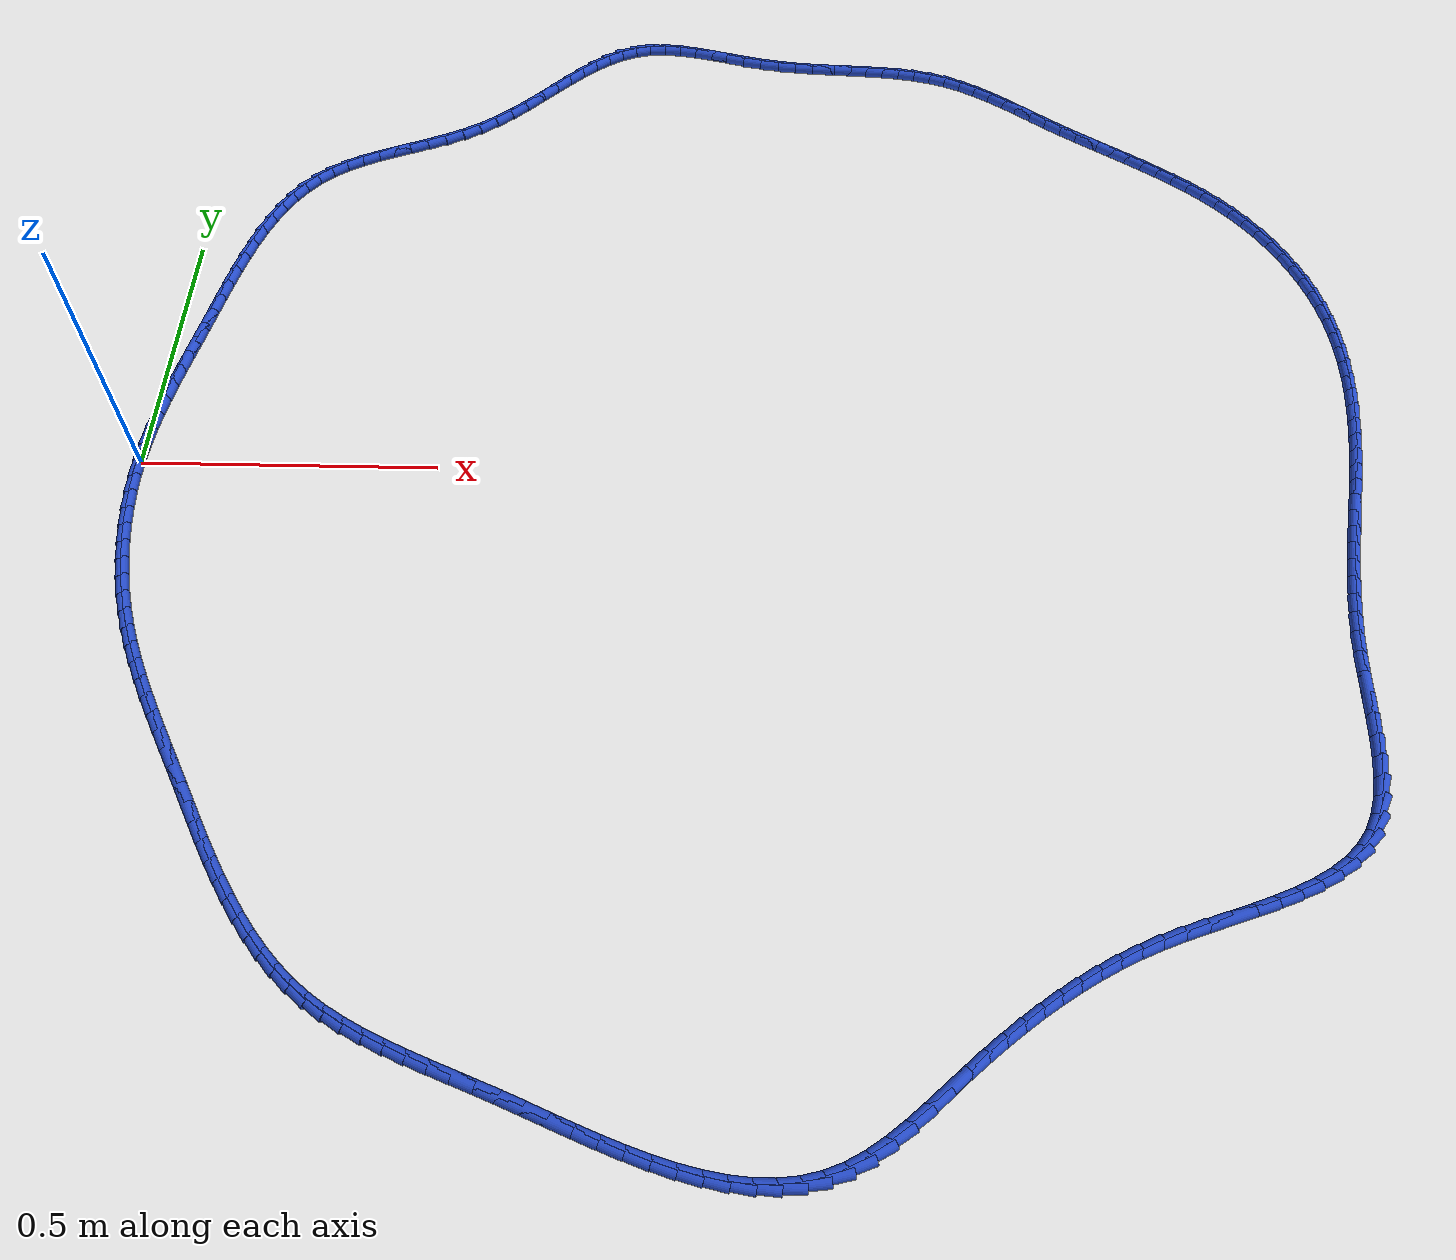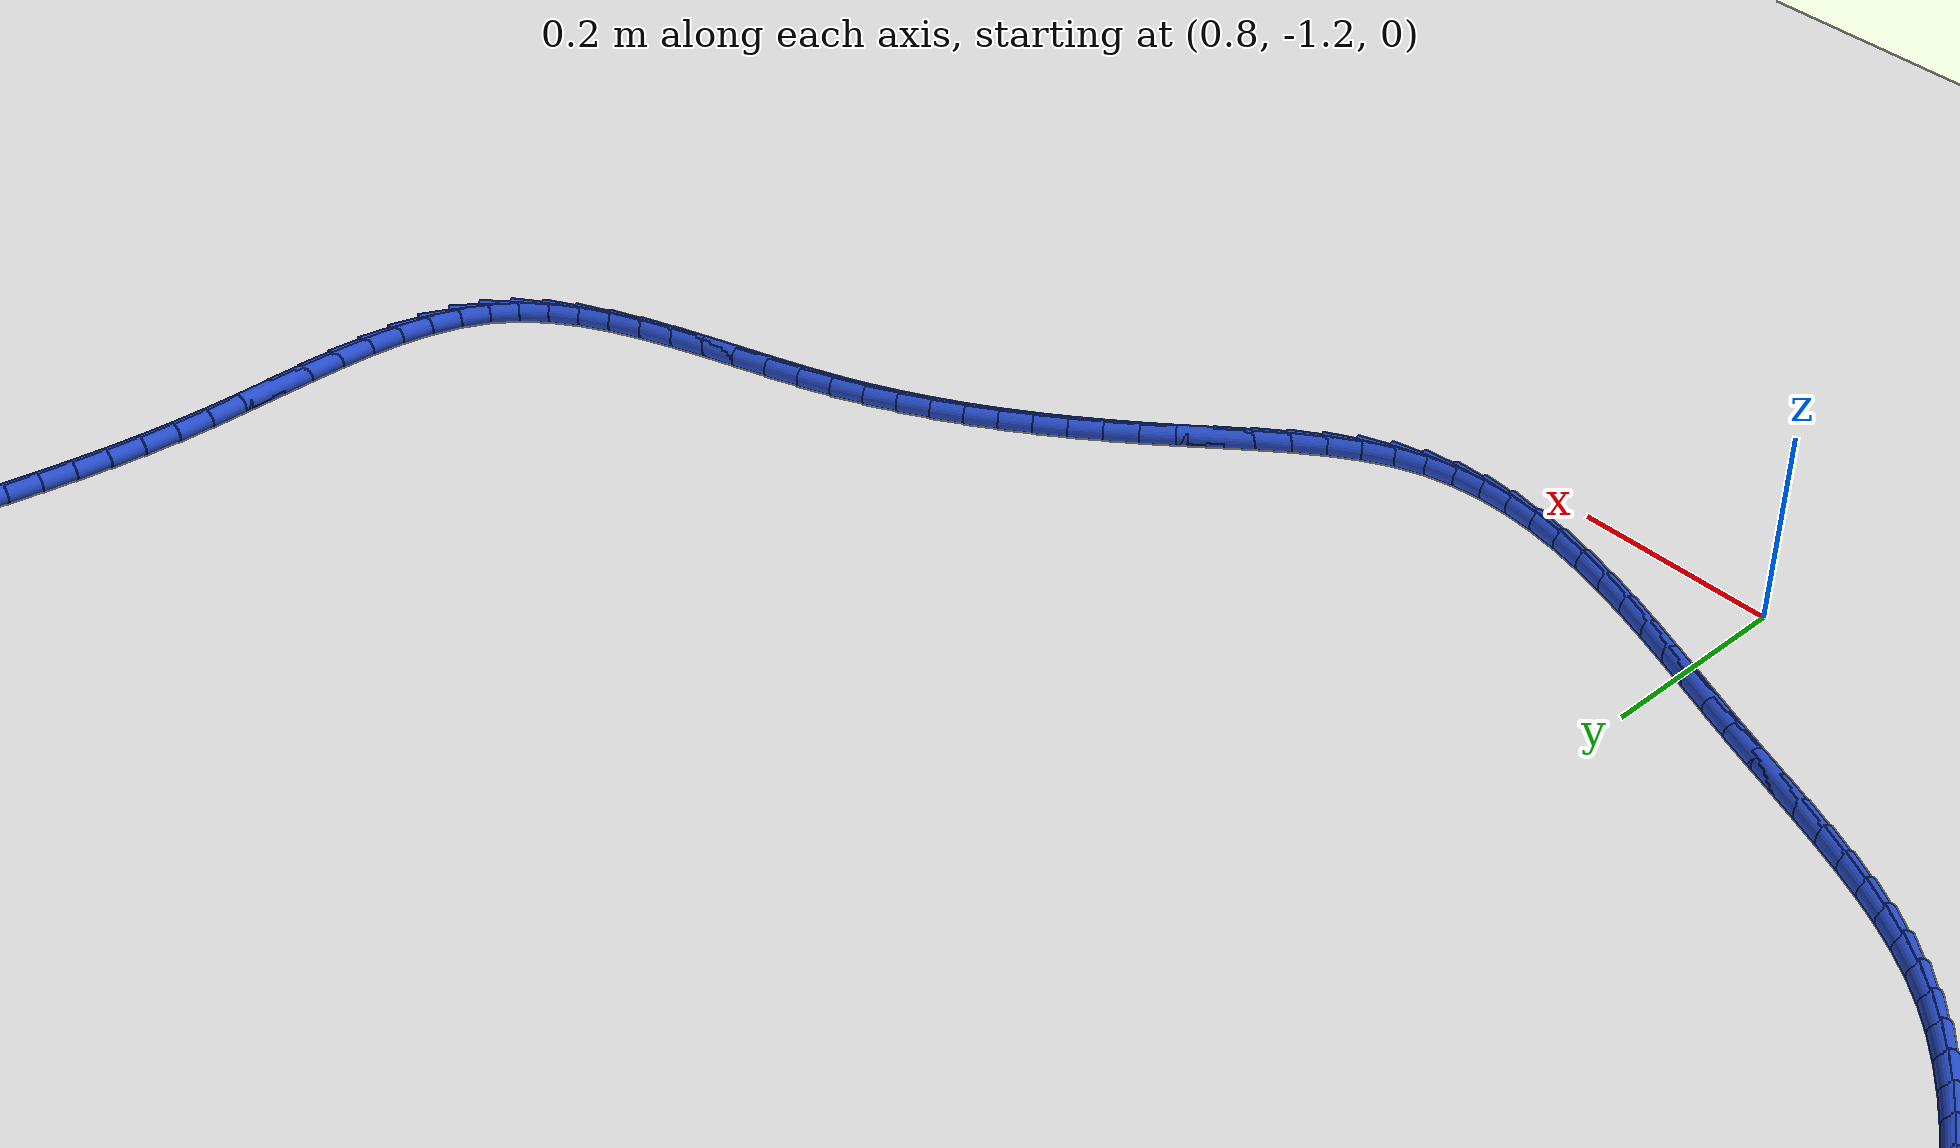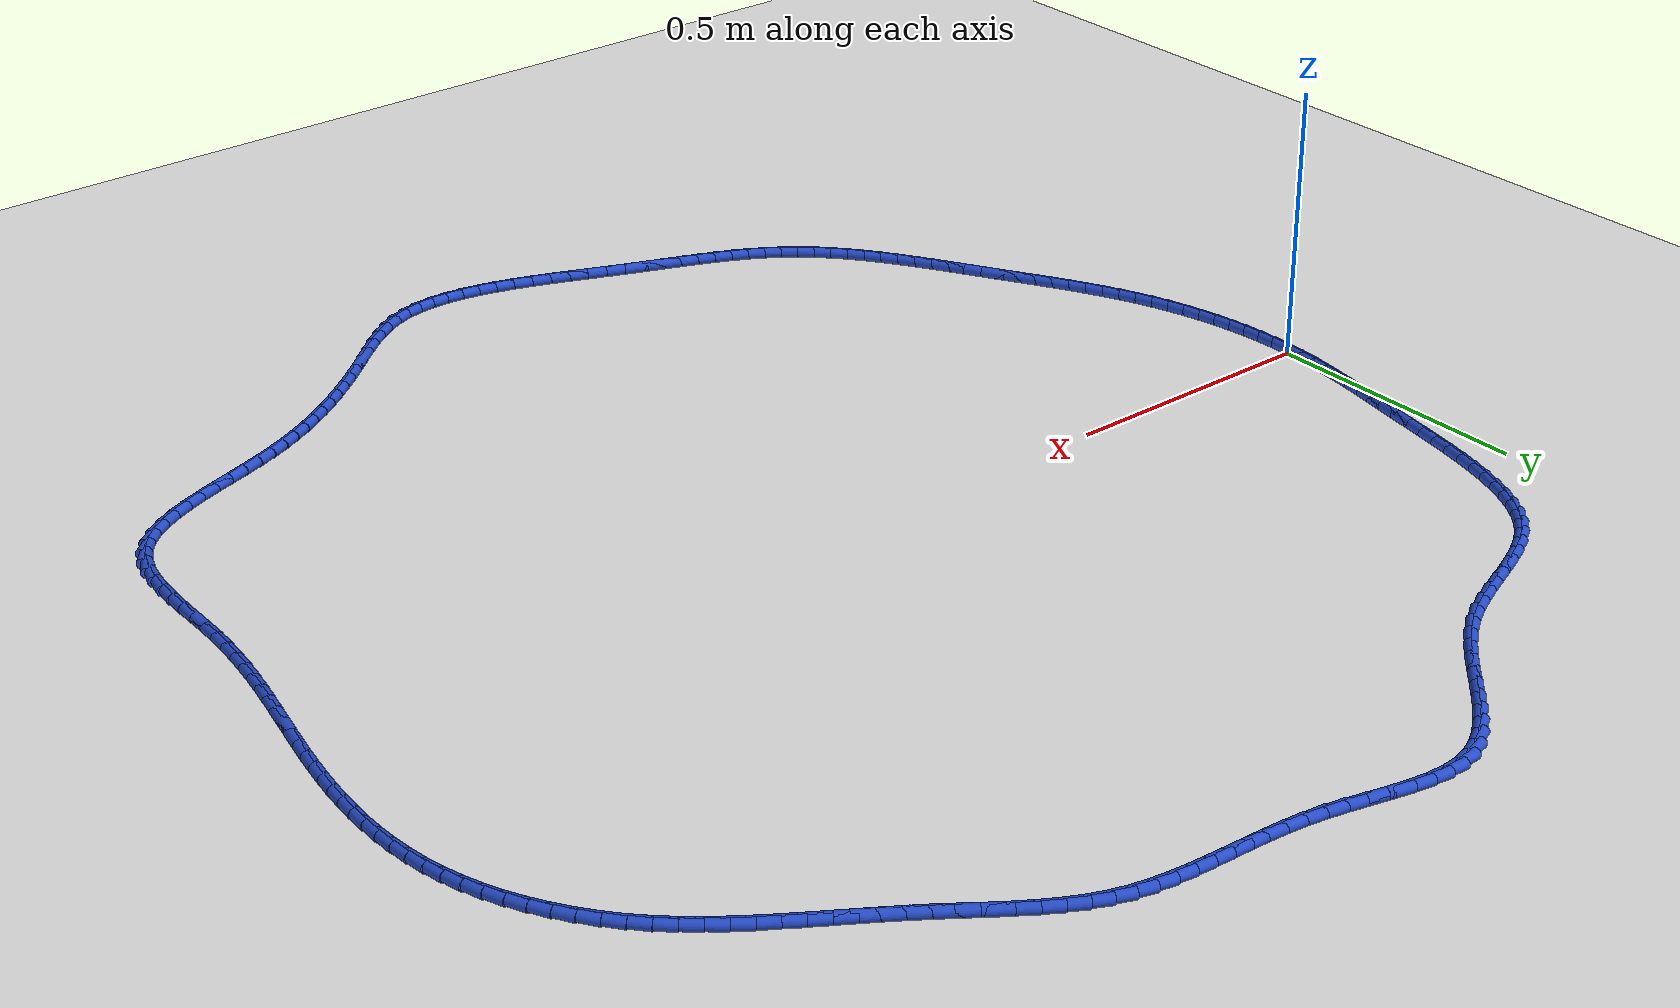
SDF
<sdf version="1.6">
 <world name="default">
  <light name="sun" type="directional">
   <pose>0 0 10 0 -0 0</pose>
   <diffuse>0.8 0.8 0.8 1</diffuse>
   <specular>0.2 0.2 0.2 1</specular>
   <attenuation>
    <range>1000</range>
    <constant>0.9</constant>
    <linear>0.01</linear>
    <quadratic>0.001</quadratic>
   </attenuation>
   <direction>-0.5 0.1 -0.9</direction>
  </light>
  <model name="ground_plane">
   <static>1</static>
   <link name="link">
    <collision name="collision">
     <geometry><plane><normal>0 0 1</normal><size>100 100</size></plane></geometry>
     <surface><friction><ode><mu>100</mu><mu2>50</mu2></ode></friction></surface>
    </collision>
    <visual name="visual">
     <cast_shadows>0</cast_shadows>
     <geometry><plane><normal>0 0 1</normal><size>100 100</size></plane></geometry>
     <material>
      <script><uri>file://media/materials/scripts/gazebo.material</uri><name>Gazebo/WhiteGlow</name></script>
     </material>
    </visual>
   </link>
  </model>
  <gravity>0 0 -9.8</gravity>
  <magnetic_field>6e-06 2.3e-05 -4.2e-05</magnetic_field>
  <atmosphere type="adiabatic"/>
  <physics name="default_physics" default="0" type="ode">
   <max_step_size>0.001</max_step_size>
   <real_time_factor>1</real_time_factor>
   <real_time_update_rate>1000</real_time_update_rate>
  </physics>
  <scene><ambient>0.4 0.4 0.4 1</ambient><background>0.7 0.7 0.7 1</background><shadows>1</shadows></scene>
  <spherical_coordinates>
   <surface_model>EARTH_WGS84</surface_model>
   <latitude_deg>0</latitude_deg>
   <longitude_deg>0</longitude_deg>
   <elevation>0</elevation>
   <heading_deg>0</heading_deg>
  </spherical_coordinates>
  <model name="line">
   <link name="link_0">
    <pose>2.0816681711721685e-17 -4.163336342344337e-17 0.01 0 1.57 1.5177850047014827</pose>
    <collision name="collision">
     <geometry><cylinder><radius>0.01</radius><length>0.08</length></cylinder></geometry>
    </collision>
    <visual name="visual">
     <material>
      <script><name>Gazebo/Blue</name><uri>file://media/materials/scripts/gazebo.material</uri></script>
     </material>
     <geometry><cylinder><radius>0.01</radius><length>0.08</length></cylinder></geometry>
    </visual>
   </link>
   <link name="link_1">
    <pose>0.0017510972646374745 0.0330015660207481 0.01 0 1.57 1.479769540509891</pose>
    <collision name="collision">
     <geometry><cylinder><radius>0.01</radius><length>0.08</length></cylinder></geometry>
    </collision>
    <visual name="visual">
     <material>
      <script><name>Gazebo/Blue</name><uri>file://media/materials/scripts/gazebo.material</uri></script>
     </material>
     <geometry><cylinder><radius>0.01</radius><length>0.08</length></cylinder></geometry>
    </visual>
   </link>
   <link name="link_2">
    <pose>0.004742166672405374 0.06576998235816929 0.01 0 1.57 1.446837215099269</pose>
    <collision name="collision">
     <geometry><cylinder><radius>0.01</radius><length>0.08</length></cylinder></geometry>
    </collision>
    <visual name="visual">
     <material>
      <script><name>Gazebo/Blue</name><uri>file://media/materials/scripts/gazebo.material</uri></script>
     </material>
     <geometry><cylinder><radius>0.01</radius><length>0.08</length></cylinder></geometry>
    </visual>
   </link>
   <link name="link_3">
    <pose>0.008809686094679404 0.09841513725901559 0.01 0 1.57 1.4193394882834067</pose>
    <collision name="collision">
     <geometry><cylinder><radius>0.01</radius><length>0.08</length></cylinder></geometry>
    </collision>
    <visual name="visual">
     <material>
      <script><name>Gazebo/Blue</name><uri>file://media/materials/scripts/gazebo.material</uri></script>
     </material>
     <geometry><cylinder><radius>0.01</radius><length>0.08</length></cylinder></geometry>
    </visual>
   </link>
   <link name="link_4">
    <pose>0.013790133402835268 0.13104691897003926 0.01 0 1.57 1.3974794756898747</pose>
    <collision name="collision">
     <geometry><cylinder><radius>0.01</radius><length>0.08</length></cylinder></geometry>
    </collision>
    <visual name="visual">
     <material>
      <script><name>Gazebo/Blue</name><uri>file://media/materials/scripts/gazebo.material</uri></script>
     </material>
     <geometry><cylinder><radius>0.01</radius><length>0.08</length></cylinder></geometry>
    </visual>
   </link>
   <link name="link_5">
    <pose>0.01951998646824864 0.1637752157379924 0.01 0 1.57 1.3813310214950196</pose>
    <collision name="collision">
     <geometry><cylinder><radius>0.01</radius><length>0.08</length></cylinder></geometry>
    </collision>
    <visual name="visual">
     <material>
      <script><name>Gazebo/Blue</name><uri>file://media/materials/scripts/gazebo.material</uri></script>
     </material>
     <geometry><cylinder><radius>0.01</radius><length>0.08</length></cylinder></geometry>
    </visual>
   </link>
   <link name="link_6">
    <pose>0.02583572316229522 0.19670991580962716 0.01 0 1.57 1.3708602117803983</pose>
    <collision name="collision">
     <geometry><cylinder><radius>0.01</radius><length>0.08</length></cylinder></geometry>
    </collision>
    <visual name="visual">
     <material>
      <script><name>Gazebo/Blue</name><uri>file://media/materials/scripts/gazebo.material</uri></script>
     </material>
     <geometry><cylinder><radius>0.01</radius><length>0.08</length></cylinder></geometry>
    </visual>
   </link>
   <link name="link_7">
    <pose>0.032573821356350716 0.2299609074316959 0.01 0 1.57 1.3659456902525984</pose>
    <collision name="collision">
     <geometry><cylinder><radius>0.01</radius><length>0.08</length></cylinder></geometry>
    </collision>
    <visual name="visual">
     <material>
      <script><name>Gazebo/Blue</name><uri>file://media/materials/scripts/gazebo.material</uri></script>
     </material>
     <geometry><cylinder><radius>0.01</radius><length>0.08</length></cylinder></geometry>
    </visual>
   </link>
   <link name="link_8">
    <pose>0.03957075892179078 0.2636380788509505 0.01 0 1.57 1.3663956872044727</pose>
    <collision name="collision">
     <geometry><cylinder><radius>0.01</radius><length>0.08</length></cylinder></geometry>
    </collision>
    <visual name="visual">
     <material>
      <script><name>Gazebo/Blue</name><uri>file://media/materials/scripts/gazebo.material</uri></script>
     </material>
     <geometry><cylinder><radius>0.01</radius><length>0.08</length></cylinder></geometry>
    </visual>
   </link>
   <link name="link_9">
    <pose>0.04666301372999114 0.29785131831414324 0.01 0 1.57 1.371274127699775</pose>
    <collision name="collision">
     <geometry><cylinder><radius>0.01</radius><length>0.08</length></cylinder></geometry>
    </collision>
    <visual name="visual">
     <material>
      <script><name>Gazebo/Blue</name><uri>file://media/materials/scripts/gazebo.material</uri></script>
     </material>
     <geometry><cylinder><radius>0.01</radius><length>0.08</length></cylinder></geometry>
    </visual>
   </link>
   <link name="link_10">
    <pose>0.05370767862764933 0.3326892224893551 0.01 0 1.57 1.3728020281031887</pose>
    <collision name="collision">
     <geometry><cylinder><radius>0.01</radius><length>0.08</length></cylinder></geometry>
    </collision>
    <visual name="visual">
     <material>
      <script><name>Gazebo/Blue</name><uri>file://media/materials/scripts/gazebo.material</uri></script>
     </material>
     <geometry><cylinder><radius>0.01</radius><length>0.08</length></cylinder></geometry>
    </visual>
   </link>
   <link name="link_11">
    <pose>0.06079230001103776 0.368002370787589 0.01 0 1.57 1.366404610873969</pose>
    <collision name="collision">
     <geometry><cylinder><radius>0.01</radius><length>0.08</length></cylinder></geometry>
    </collision>
    <visual name="visual">
     <material>
      <script><name>Gazebo/Blue</name><uri>file://media/materials/scripts/gazebo.material</uri></script>
     </material>
     <geometry><cylinder><radius>0.01</radius><length>0.08</length></cylinder></geometry>
    </visual>
   </link>
   <link name="link_12">
    <pose>0.06814885094772555 0.40349217572606627 0.01 0 1.57 1.3520287828510378</pose>
    <collision name="collision">
     <geometry><cylinder><radius>0.01</radius><length>0.08</length></cylinder></geometry>
    </collision>
    <visual name="visual">
     <material>
      <script><name>Gazebo/Blue</name><uri>file://media/materials/scripts/gazebo.material</uri></script>
     </material>
     <geometry><cylinder><radius>0.01</radius><length>0.08</length></cylinder></geometry>
    </visual>
   </link>
   <link name="link_13">
    <pose>0.07601152755418306 0.43885775381050113 0.01 0 1.57 1.3293796384983325</pose>
    <collision name="collision">
     <geometry><cylinder><radius>0.01</radius><length>0.08</length></cylinder></geometry>
    </collision>
    <visual name="visual">
     <material>
      <script><name>Gazebo/Blue</name><uri>file://media/materials/scripts/gazebo.material</uri></script>
     </material>
     <geometry><cylinder><radius>0.01</radius><length>0.08</length></cylinder></geometry>
    </visual>
   </link>
   <link name="link_14">
    <pose>0.08461452594688063 0.4737982215466072 0.01 0 1.57 1.2978563678131796</pose>
    <collision name="collision">
     <geometry><cylinder><radius>0.01</radius><length>0.08</length></cylinder></geometry>
    </collision>
    <visual name="visual">
     <material>
      <script><name>Gazebo/Blue</name><uri>file://media/materials/scripts/gazebo.material</uri></script>
     </material>
     <geometry><cylinder><radius>0.01</radius><length>0.08</length></cylinder></geometry>
    </visual>
   </link>
   <link name="link_15">
    <pose>0.09419204224228851 0.5080126954400984 0.01 0 1.57 1.2565573028411883</pose>
    <collision name="collision">
     <geometry><cylinder><radius>0.01</radius><length>0.08</length></cylinder></geometry>
    </collision>
    <visual name="visual">
     <material>
      <script><name>Gazebo/Blue</name><uri>file://media/materials/scripts/gazebo.material</uri></script>
     </material>
     <geometry><cylinder><radius>0.01</radius><length>0.08</length></cylinder></geometry>
    </visual>
   </link>
   <link name="link_16">
    <pose>0.10497827255687715 0.5412002919966886 0.01 0 1.57 1.2042964606648994</pose>
    <collision name="collision">
     <geometry><cylinder><radius>0.01</radius><length>0.08</length></cylinder></geometry>
    </collision>
    <visual name="visual">
     <material>
      <script><name>Gazebo/Blue</name><uri>file://media/materials/scripts/gazebo.material</uri></script>
     </material>
     <geometry><cylinder><radius>0.01</radius><length>0.08</length></cylinder></geometry>
    </visual>
   </link>
   <link name="link_17">
    <pose>0.11720741300711682 0.5730601277220915 0.01 0 1.57 1.1396603528509097</pose>
    <collision name="collision">
     <geometry><cylinder><radius>0.01</radius><length>0.08</length></cylinder></geometry>
    </collision>
    <visual name="visual">
     <material>
      <script><name>Gazebo/Blue</name><uri>file://media/materials/scripts/gazebo.material</uri></script>
     </material>
     <geometry><cylinder><radius>0.01</radius><length>0.08</length></cylinder></geometry>
    </visual>
   </link>
   <link name="link_18">
    <pose>0.13111365970947786 0.6032913191220214 0.01 0 1.57 1.0611525408388207</pose>
    <collision name="collision">
     <geometry><cylinder><radius>0.01</radius><length>0.08</length></cylinder></geometry>
    </collision>
    <visual name="visual">
     <material>
      <script><name>Gazebo/Blue</name><uri>file://media/materials/scripts/gazebo.material</uri></script>
     </material>
     <geometry><cylinder><radius>0.01</radius><length>0.08</length></cylinder></geometry>
    </visual>
   </link>
   <link name="link_19">
    <pose>0.1469312087804306 0.6315929827021914 0.01 0 1.57 0.9674923032002456</pose>
    <collision name="collision">
     <geometry><cylinder><radius>0.01</radius><length>0.08</length></cylinder></geometry>
    </collision>
    <visual name="visual">
     <material>
      <script><name>Gazebo/Blue</name><uri>file://media/materials/scripts/gazebo.material</uri></script>
     </material>
     <geometry><cylinder><radius>0.01</radius><length>0.08</length></cylinder></geometry>
    </visual>
   </link>
   <link name="link_20">
    <pose>0.1648942563364455 0.6576642349683164 0.01 0 1.57 0.8581278723258284</pose>
    <collision name="collision">
     <geometry><cylinder><radius>0.01</radius><length>0.08</length></cylinder></geometry>
    </collision>
    <visual name="visual">
     <material>
      <script><name>Gazebo/Blue</name><uri>file://media/materials/scripts/gazebo.material</uri></script>
     </material>
     <geometry><cylinder><radius>0.01</radius><length>0.08</length></cylinder></geometry>
    </visual>
   </link>
   <link name="link_21">
    <pose>0.18523699849399264 0.6812041924261092 0.01 0 1.57 0.7340215848732757</pose>
    <collision name="collision">
     <geometry><cylinder><radius>0.01</radius><length>0.08</length></cylinder></geometry>
    </collision>
    <visual name="visual">
     <material>
      <script><name>Gazebo/Blue</name><uri>file://media/materials/scripts/gazebo.material</uri></script>
     </material>
     <geometry><cylinder><radius>0.01</radius><length>0.08</length></cylinder></geometry>
    </visual>
   </link>
   <link name="link_22">
    <pose>0.20819213259728347 0.7019139955489478 0.01 0 1.57 0.6095088317651606</pose>
    <collision name="collision">
     <geometry><cylinder><radius>0.01</radius><length>0.08</length></cylinder></geometry>
    </collision>
    <visual name="visual">
     <material>
      <script><name>Gazebo/Blue</name><uri>file://media/materials/scripts/gazebo.material</uri></script>
     </material>
     <geometry><cylinder><radius>0.01</radius><length>0.08</length></cylinder></geometry>
    </visual>
   </link>
   <link name="link_23">
    <pose>0.23378117936892437 0.7197799613276896 0.01 0 1.57 0.5107004905849902</pose>
    <collision name="collision">
     <geometry><cylinder><radius>0.01</radius><length>0.08</length></cylinder></geometry>
    </collision>
    <visual name="visual">
     <material>
      <script><name>Gazebo/Blue</name><uri>file://media/materials/scripts/gazebo.material</uri></script>
     </material>
     <geometry><cylinder><radius>0.01</radius><length>0.08</length></cylinder></geometry>
    </visual>
   </link>
   <link name="link_24">
    <pose>0.2615984139893411 0.7353653664322631 0.01 0 1.57 0.4402278030746432</pose>
    <collision name="collision">
     <geometry><cylinder><radius>0.01</radius><length>0.08</length></cylinder></geometry>
    </collision>
    <visual name="visual">
     <material>
      <script><name>Gazebo/Blue</name><uri>file://media/materials/scripts/gazebo.material</uri></script>
     </material>
     <geometry><cylinder><radius>0.01</radius><length>0.08</length></cylinder></geometry>
    </visual>
   </link>
   <link name="link_25">
    <pose>0.2911865486383726 0.7493031190894743 0.01 0 1.57 0.396094104812414</pose>
    <collision name="collision">
     <geometry><cylinder><radius>0.01</radius><length>0.08</length></cylinder></geometry>
    </collision>
    <visual name="visual">
     <material>
      <script><name>Gazebo/Blue</name><uri>file://media/materials/scripts/gazebo.material</uri></script>
     </material>
     <geometry><cylinder><radius>0.01</radius><length>0.08</length></cylinder></geometry>
    </visual>
   </link>
   <link name="link_26">
    <pose>0.3220882954958574 0.7622261275261286 0.01 0 1.57 0.37609965970879766</pose>
    <collision name="collision">
     <geometry><cylinder><radius>0.01</radius><length>0.08</length></cylinder></geometry>
    </collision>
    <visual name="visual">
     <material>
      <script><name>Gazebo/Blue</name><uri>file://media/materials/scripts/gazebo.material</uri></script>
     </material>
     <geometry><cylinder><radius>0.01</radius><length>0.08</length></cylinder></geometry>
    </visual>
   </link>
   <link name="link_27">
    <pose>0.3538463667416338 0.7747672999690318 0.01 0 1.57 0.3786123395951158</pose>
    <collision name="collision">
     <geometry><cylinder><radius>0.01</radius><length>0.08</length></cylinder></geometry>
    </collision>
    <visual name="visual">
     <material>
      <script><name>Gazebo/Blue</name><uri>file://media/materials/scripts/gazebo.material</uri></script>
     </material>
     <geometry><cylinder><radius>0.01</radius><length>0.08</length></cylinder></geometry>
    </visual>
   </link>
   <link name="link_28">
    <pose>0.3860034745555406 0.7875595446449892 0.01 0 1.57 0.402773046746959</pose>
    <collision name="collision">
     <geometry><cylinder><radius>0.01</radius><length>0.08</length></cylinder></geometry>
    </collision>
    <visual name="visual">
     <material>
      <script><name>Gazebo/Blue</name><uri>file://media/materials/scripts/gazebo.material</uri></script>
     </material>
     <geometry><cylinder><radius>0.01</radius><length>0.08</length></cylinder></geometry>
    </visual>
   </link>
   <link name="link_29">
    <pose>0.4181023311174161 0.8012357697808068 0.01 0 1.57 0.4483719509029207</pose>
    <collision name="collision">
     <geometry><cylinder><radius>0.01</radius><length>0.08</length></cylinder></geometry>
    </collision>
    <visual name="visual">
     <material>
      <script><name>Gazebo/Blue</name><uri>file://media/materials/scripts/gazebo.material</uri></script>
     </material>
     <geometry><cylinder><radius>0.01</radius><length>0.08</length></cylinder></geometry>
    </visual>
   </link>
   <link name="link_30">
    <pose>0.44968564860709925 0.8164288836032901 0.01 0 1.57 0.5154739808662969</pose>
    <collision name="collision">
     <geometry><cylinder><radius>0.01</radius><length>0.08</length></cylinder></geometry>
    </collision>
    <visual name="visual">
     <material>
      <script><name>Gazebo/Blue</name><uri>file://media/materials/scripts/gazebo.material</uri></script>
     </material>
     <geometry><cylinder><radius>0.01</radius><length>0.08</length></cylinder></geometry>
    </visual>
   </link>
   <link name="link_31">
    <pose>0.48029613920442826 0.8337717943392445 0.01 0 1.57 0.6013774213515227</pose>
    <collision name="collision">
     <geometry><cylinder><radius>0.01</radius><length>0.08</length></cylinder></geometry>
    </collision>
    <visual name="visual">
     <material>
      <script><name>Gazebo/Blue</name><uri>file://media/materials/scripts/gazebo.material</uri></script>
     </material>
     <geometry><cylinder><radius>0.01</radius><length>0.08</length></cylinder></geometry>
    </visual>
   </link>
   <link name="link_32">
    <pose>0.5095168344874591 0.853821890895861 0.01 0 1.57 0.6799014885389717</pose>
    <collision name="collision">
     <geometry><cylinder><radius>0.01</radius><length>0.08</length></cylinder></geometry>
    </collision>
    <visual name="visual">
     <material>
      <script><name>Gazebo/Blue</name><uri>file://media/materials/scripts/gazebo.material</uri></script>
     </material>
     <geometry><cylinder><radius>0.01</radius><length>0.08</length></cylinder></geometry>
    </visual>
   </link>
   <link name="link_33">
    <pose>0.5373598314949672 0.8763329110075202 0.01 0 1.57 0.7364725211335498</pose>
    <collision name="collision">
     <geometry><cylinder><radius>0.01</radius><length>0.08</length></cylinder></geometry>
    </collision>
    <visual name="visual">
     <material>
      <script><name>Gazebo/Blue</name><uri>file://media/materials/scripts/gazebo.material</uri></script>
     </material>
     <geometry><cylinder><radius>0.01</radius><length>0.08</length></cylinder></geometry>
    </visual>
   </link>
   <link name="link_34">
    <pose>0.5640963110389123 0.9005733215181787 0.01 0 1.57 0.7722344801264491</pose>
    <collision name="collision">
     <geometry><cylinder><radius>0.01</radius><length>0.08</length></cylinder></geometry>
    </collision>
    <visual name="visual">
     <material>
      <script><name>Gazebo/Blue</name><uri>file://media/materials/scripts/gazebo.material</uri></script>
     </material>
     <geometry><cylinder><radius>0.01</radius><length>0.08</length></cylinder></geometry>
    </visual>
   </link>
   <link name="link_35">
    <pose>0.5900010409240547 0.925804870737593 0.01 0 1.57 0.7880871660311061</pose>
    <collision name="collision">
     <geometry><cylinder><radius>0.01</radius><length>0.08</length></cylinder></geometry>
    </collision>
    <visual name="visual">
     <material>
      <script><name>Gazebo/Blue</name><uri>file://media/materials/scripts/gazebo.material</uri></script>
     </material>
     <geometry><cylinder><radius>0.01</radius><length>0.08</length></cylinder></geometry>
    </visual>
   </link>
   <link name="link_36">
    <pose>0.615348788955155 0.9512893069755195 0.01 0 1.57 0.7840706311847844</pose>
    <collision name="collision">
     <geometry><cylinder><radius>0.01</radius><length>0.08</length></cylinder></geometry>
    </collision>
    <visual name="visual">
     <material>
      <script><name>Gazebo/Blue</name><uri>file://media/materials/scripts/gazebo.material</uri></script>
     </material>
     <geometry><cylinder><radius>0.01</radius><length>0.08</length></cylinder></geometry>
    </visual>
   </link>
   <link name="link_37">
    <pose>0.6404143229369739 0.9762883785417159 0.01 0 1.57 0.7591388009299431</pose>
    <collision name="collision">
     <geometry><cylinder><radius>0.01</radius><length>0.08</length></cylinder></geometry>
    </collision>
    <visual name="visual">
     <material>
      <script><name>Gazebo/Blue</name><uri>file://media/materials/scripts/gazebo.material</uri></script>
     </material>
     <geometry><cylinder><radius>0.01</radius><length>0.08</length></cylinder></geometry>
    </visual>
   </link>
   <link name="link_38">
    <pose>0.6654724106742717 1.0000638337459382 0.01 0 1.57 0.7110362355102086</pose>
    <collision name="collision">
     <geometry><cylinder><radius>0.01</radius><length>0.08</length></cylinder></geometry>
    </collision>
    <visual name="visual">
     <material>
      <script><name>Gazebo/Blue</name><uri>file://media/materials/scripts/gazebo.material</uri></script>
     </material>
     <geometry><cylinder><radius>0.01</radius><length>0.08</length></cylinder></geometry>
    </visual>
   </link>
   <link name="link_39">
    <pose>0.690797819971809 1.0218774208979435 0.01 0 1.57 0.6363584933995068</pose>
    <collision name="collision">
     <geometry><cylinder><radius>0.01</radius><length>0.08</length></cylinder></geometry>
    </collision>
    <visual name="visual">
     <material>
      <script><name>Gazebo/Blue</name><uri>file://media/materials/scripts/gazebo.material</uri></script>
     </material>
     <geometry><cylinder><radius>0.01</radius><length>0.08</length></cylinder></geometry>
    </visual>
   </link>
   <link name="link_40">
    <pose>0.7166653186343466 1.0409908883074888 0.01 0 1.57 0.5311229275402451</pose>
    <collision name="collision">
     <geometry><cylinder><radius>0.01</radius><length>0.08</length></cylinder></geometry>
    </collision>
    <visual name="visual">
     <material>
      <script><name>Gazebo/Blue</name><uri>file://media/materials/scripts/gazebo.material</uri></script>
     </material>
     <geometry><cylinder><radius>0.01</radius><length>0.08</length></cylinder></geometry>
    </visual>
   </link>
   <link name="link_41">
    <pose>0.7433496744666444 1.0566659842843302 0.01 0 1.57 0.3924927095049018</pose>
    <collision name="collision">
     <geometry><cylinder><radius>0.01</radius><length>0.08</length></cylinder></geometry>
    </collision>
    <visual name="visual">
     <material>
      <script><name>Gazebo/Blue</name><uri>file://media/materials/scripts/gazebo.material</uri></script>
     </material>
     <geometry><cylinder><radius>0.01</radius><length>0.08</length></cylinder></geometry>
    </visual>
   </link>
   <link name="link_42">
    <pose>0.7711256552734631 1.068164457138225 0.01 0 1.57 0.22272313533182245</pose>
    <collision name="collision">
     <geometry><cylinder><radius>0.01</radius><length>0.08</length></cylinder></geometry>
    </collision>
    <visual name="visual">
     <material>
      <script><name>Gazebo/Blue</name><uri>file://media/materials/scripts/gazebo.material</uri></script>
     </material>
     <geometry><cylinder><radius>0.01</radius><length>0.08</length></cylinder></geometry>
    </visual>
   </link>
   <link name="link_43">
    <pose>0.8002636502832967 1.074763644184522 0.01 0 1.57 0.05439537003679868</pose>
    <collision name="collision">
     <geometry><cylinder><radius>0.01</radius><length>0.08</length></cylinder></geometry>
    </collision>
    <visual name="visual">
     <material>
      <script><name>Gazebo/Blue</name><uri>file://media/materials/scripts/gazebo.material</uri></script>
     </material>
     <geometry><cylinder><radius>0.01</radius><length>0.08</length></cylinder></geometry>
    </visual>
   </link>
   <link name="link_44">
    <pose>0.8308409002792685 1.0764285474065474 0.01 0 1.57 -0.07403487739956499</pose>
    <collision name="collision">
     <geometry><cylinder><radius>0.01</radius><length>0.08</length></cylinder></geometry>
    </collision>
    <visual name="visual">
     <material>
      <script><name>Gazebo/Blue</name><uri>file://media/materials/scripts/gazebo.material</uri></script>
     </material>
     <geometry><cylinder><radius>0.01</radius><length>0.08</length></cylinder></geometry>
    </visual>
   </link>
   <link name="link_45">
    <pose>0.8626696031833289 1.074067798495755 0.01 0 1.57 -0.16309145519003512</pose>
    <collision name="collision">
     <geometry><cylinder><radius>0.01</radius><length>0.08</length></cylinder></geometry>
    </collision>
    <visual name="visual">
     <material>
      <script><name>Gazebo/Blue</name><uri>file://media/materials/scripts/gazebo.material</uri></script>
     </material>
     <geometry><cylinder><radius>0.01</radius><length>0.08</length></cylinder></geometry>
    </visual>
   </link>
   <link name="link_46">
    <pose>0.8955427466088771 1.0686584234318646 0.01 0 1.57 -0.21837881261023018</pose>
    <collision name="collision">
     <geometry><cylinder><radius>0.01</radius><length>0.08</length></cylinder></geometry>
    </collision>
    <visual name="visual">
     <material>
      <script><name>Gazebo/Blue</name><uri>file://media/materials/scripts/gazebo.material</uri></script>
     </material>
     <geometry><cylinder><radius>0.01</radius><length>0.08</length></cylinder></geometry>
    </visual>
   </link>
   <link name="link_47">
    <pose>0.9292533181693131 1.0611774481945955 0.01 0 1.57 -0.24471287090163552</pose>
    <collision name="collision">
     <geometry><cylinder><radius>0.01</radius><length>0.08</length></cylinder></geometry>
    </collision>
    <visual name="visual">
     <material>
      <script><name>Gazebo/Blue</name><uri>file://media/materials/scripts/gazebo.material</uri></script>
     </material>
     <geometry><cylinder><radius>0.01</radius><length>0.08</length></cylinder></geometry>
    </visual>
   </link>
   <link name="link_48">
    <pose>0.9635943054780363 1.0526018987636678 0.01 0 1.57 -0.24503280778536315</pose>
    <collision name="collision">
     <geometry><cylinder><radius>0.01</radius><length>0.08</length></cylinder></geometry>
    </collision>
    <visual name="visual">
     <material>
      <script><name>Gazebo/Blue</name><uri>file://media/materials/scripts/gazebo.material</uri></script>
     </material>
     <geometry><cylinder><radius>0.01</radius><length>0.08</length></cylinder></geometry>
    </visual>
   </link>
   <link name="link_49">
    <pose>0.9983586961484471 1.0439088011188016 0.01 0 1.57 -0.22030593380127114</pose>
    <collision name="collision">
     <geometry><cylinder><radius>0.01</radius><length>0.08</length></cylinder></geometry>
    </collision>
    <visual name="visual">
     <material>
      <script><name>Gazebo/Blue</name><uri>file://media/materials/scripts/gazebo.material</uri></script>
     </material>
     <geometry><cylinder><radius>0.01</radius><length>0.08</length></cylinder></geometry>
    </visual>
   </link>
   <link name="link_50">
    <pose>1.0333394777939446 1.0360751812397158 0.01 0 1.57 -0.1721621666128202</pose>
    <collision name="collision">
     <geometry><cylinder><radius>0.01</radius><length>0.08</length></cylinder></geometry>
    </collision>
    <visual name="visual">
     <material>
      <script><name>Gazebo/Blue</name><uri>file://media/materials/scripts/gazebo.material</uri></script>
     </material>
     <geometry><cylinder><radius>0.01</radius><length>0.08</length></cylinder></geometry>
    </visual>
   </link>
   <link name="link_51">
    <pose>1.068337598693716 1.029989584460974 0.01 0 1.57 -0.12309830729193323</pose>
    <collision name="collision">
     <geometry><cylinder><radius>0.01</radius><length>0.08</length></cylinder></geometry>
    </collision>
    <visual name="visual">
     <material>
      <script><name>Gazebo/Blue</name><uri>file://media/materials/scripts/gazebo.material</uri></script>
     </material>
     <geometry><cylinder><radius>0.01</radius><length>0.08</length></cylinder></geometry>
    </visual>
   </link>
   <link name="link_52">
    <pose>1.1032321248833863 1.0256722984018283 0.01 0 1.57 -0.08680786731950309</pose>
    <collision name="collision">
     <geometry><cylinder><radius>0.01</radius><length>0.08</length></cylinder></geometry>
    </collision>
    <visual name="visual">
     <material>
      <script><name>Gazebo/Blue</name><uri>file://media/materials/scripts/gazebo.material</uri></script>
     </material>
     <geometry><cylinder><radius>0.01</radius><length>0.08</length></cylinder></geometry>
    </visual>
   </link>
   <link name="link_53">
    <pose>1.1379464220578168 1.02265123196165 0.01 0 1.57 -0.06383379521660654</pose>
    <collision name="collision">
     <geometry><cylinder><radius>0.01</radius><length>0.08</length></cylinder></geometry>
    </collision>
    <visual name="visual">
     <material>
      <script><name>Gazebo/Blue</name><uri>file://media/materials/scripts/gazebo.material</uri></script>
     </material>
     <geometry><cylinder><radius>0.01</radius><length>0.08</length></cylinder></geometry>
    </visual>
   </link>
   <link name="link_54">
    <pose>1.1724043629581593 1.0204486583575316 0.01 0 1.57 -0.054503697078604765</pose>
    <collision name="collision">
     <geometry><cylinder><radius>0.01</radius><length>0.08</length></cylinder></geometry>
    </collision>
    <visual name="visual">
     <material>
      <script><name>Gazebo/Blue</name><uri>file://media/materials/scripts/gazebo.material</uri></script>
     </material>
     <geometry><cylinder><radius>0.01</radius><length>0.08</length></cylinder></geometry>
    </visual>
   </link>
   <link name="link_55">
    <pose>1.2065298203255672 1.0185868508065683 0.01 0 1.57 -0.05921170057310159</pose>
    <collision name="collision">
     <geometry><cylinder><radius>0.01</radius><length>0.08</length></cylinder></geometry>
    </collision>
    <visual name="visual">
     <material>
      <script><name>Gazebo/Blue</name><uri>file://media/materials/scripts/gazebo.material</uri></script>
     </material>
     <geometry><cylinder><radius>0.01</radius><length>0.08</length></cylinder></geometry>
    </visual>
   </link>
   <link name="link_56">
    <pose>1.2402466669011938 1.016588082525853 0.01 0 1.57 -0.07848096469890384</pose>
    <collision name="collision">
     <geometry><cylinder><radius>0.01</radius><length>0.08</length></cylinder></geometry>
    </collision>
    <visual name="visual">
     <material>
      <script><name>Gazebo/Blue</name><uri>file://media/materials/scripts/gazebo.material</uri></script>
     </material>
     <geometry><cylinder><radius>0.01</radius><length>0.08</length></cylinder></geometry>
    </visual>
   </link>
   <link name="link_57">
    <pose>1.2734787754261914 1.0139746267324798 0.01 0 1.57 -0.11294636685541154</pose>
    <collision name="collision">
     <geometry><cylinder><radius>0.01</radius><length>0.08</length></cylinder></geometry>
    </collision>
    <visual name="visual">
     <material>
      <script><name>Gazebo/Blue</name><uri>file://media/materials/scripts/gazebo.material</uri></script>
     </material>
     <geometry><cylinder><radius>0.01</radius><length>0.08</length></cylinder></geometry>
    </visual>
   </link>
   <link name="link_58">
    <pose>1.3061500186417132 1.010268756643543 0.01 0 1.57 -0.1632336466313724</pose>
    <collision name="collision">
     <geometry><cylinder><radius>0.01</radius><length>0.08</length></cylinder></geometry>
    </collision>
    <visual name="visual">
     <material>
      <script><name>Gazebo/Blue</name><uri>file://media/materials/scripts/gazebo.material</uri></script>
     </material>
     <geometry><cylinder><radius>0.01</radius><length>0.08</length></cylinder></geometry>
    </visual>
   </link>
   <link name="link_59">
    <pose>1.3381842692889123 1.0049927454761358 0.01 0 1.57 -0.22970468994152532</pose>
    <collision name="collision">
     <geometry><cylinder><radius>0.01</radius><length>0.08</length></cylinder></geometry>
    </collision>
    <visual name="visual">
     <material>
      <script><name>Gazebo/Blue</name><uri>file://media/materials/scripts/gazebo.material</uri></script>
     </material>
     <geometry><cylinder><radius>0.01</radius><length>0.08</length></cylinder></geometry>
    </visual>
   </link>
   <link name="link_60">
    <pose>1.369505400108941 0.9976688664473518 0.01 0 1.57 -0.3120563289927454</pose>
    <collision name="collision">
     <geometry><cylinder><radius>0.01</radius><length>0.08</length></cylinder></geometry>
    </collision>
    <visual name="visual">
     <material>
      <script><name>Gazebo/Blue</name><uri>file://media/materials/scripts/gazebo.material</uri></script>
     </material>
     <geometry><cylinder><radius>0.01</radius><length>0.08</length></cylinder></geometry>
    </visual>
   </link>
   <link name="link_61">
    <pose>1.4000372838429531 0.9878193927742857 0.01 0 1.57 -0.4043626671043744</pose>
    <collision name="collision">
     <geometry><cylinder><radius>0.01</radius><length>0.08</length></cylinder></geometry>
    </collision>
    <visual name="visual">
     <material>
      <script><name>Gazebo/Blue</name><uri>file://media/materials/scripts/gazebo.material</uri></script>
     </material>
     <geometry><cylinder><radius>0.01</radius><length>0.08</length></cylinder></geometry>
    </visual>
   </link>
   <link name="link_62">
    <pose>1.429738542899711 0.9751088795616992 0.01 0 1.57 -0.48425307173069393</pose>
    <collision name="collision">
     <geometry><cylinder><radius>0.01</radius><length>0.08</length></cylinder></geometry>
    </collision>
    <visual name="visual">
     <material>
      <script><name>Gazebo/Blue</name><uri>file://media/materials/scripts/gazebo.material</uri></script>
     </material>
     <geometry><cylinder><radius>0.01</radius><length>0.08</length></cylinder></geometry>
    </visual>
   </link>
   <link name="link_63">
    <pose>1.4587283840570773 0.9598593917191135 0.01 0 1.57 -0.5458357475777404</pose>
    <collision name="collision">
     <geometry><cylinder><radius>0.01</radius><length>0.08</length></cylinder></geometry>
    </collision>
    <visual name="visual">
     <material>
      <script><name>Gazebo/Blue</name><uri>file://media/materials/scripts/gazebo.material</uri></script>
     </material>
     <geometry><cylinder><radius>0.01</radius><length>0.08</length></cylinder></geometry>
    </visual>
   </link>
   <link name="link_64">
    <pose>1.4871723692040355 0.9425827943229845 0.01 0 1.57 -0.5900398026535582</pose>
    <collision name="collision">
     <geometry><cylinder><radius>0.01</radius><length>0.08</length></cylinder></geometry>
    </collision>
    <visual name="visual">
     <material>
      <script><name>Gazebo/Blue</name><uri>file://media/materials/scripts/gazebo.material</uri></script>
     </material>
     <geometry><cylinder><radius>0.01</radius><length>0.08</length></cylinder></geometry>
    </visual>
   </link>
   <link name="link_65">
    <pose>1.5152360646995624 0.923790970752076 0.01 0 1.57 -0.6179403597329888</pose>
    <collision name="collision">
     <geometry><cylinder><radius>0.01</radius><length>0.08</length></cylinder></geometry>
    </collision>
    <visual name="visual">
     <material>
      <script><name>Gazebo/Blue</name><uri>file://media/materials/scripts/gazebo.material</uri></script>
     </material>
     <geometry><cylinder><radius>0.01</radius><length>0.08</length></cylinder></geometry>
    </visual>
   </link>
   <link name="link_66">
    <pose>1.5430850369026345 0.9039958043851513 0.01 0 1.57 -0.6304078552292787</pose>
    <collision name="collision">
     <geometry><cylinder><radius>0.01</radius><length>0.08</length></cylinder></geometry>
    </collision>
    <visual name="visual">
     <material>
      <script><name>Gazebo/Blue</name><uri>file://media/materials/scripts/gazebo.material</uri></script>
     </material>
     <geometry><cylinder><radius>0.01</radius><length>0.08</length></cylinder></geometry>
    </visual>
   </link>
   <link name="link_67">
    <pose>1.5708848521722292 0.8837091786009742 0.01 0 1.57 -0.6279404243253499</pose>
    <collision name="collision">
     <geometry><cylinder><radius>0.01</radius><length>0.08</length></cylinder></geometry>
    </collision>
    <visual name="visual">
     <material>
      <script><name>Gazebo/Blue</name><uri>file://media/materials/scripts/gazebo.material</uri></script>
     </material>
     <geometry><cylinder><radius>0.01</radius><length>0.08</length></cylinder></geometry>
    </visual>
   </link>
   <link name="link_68">
    <pose>1.5988010768673222 0.8634429767783078 0.01 0 1.57 -0.6113370738521648</pose>
    <collision name="collision">
     <geometry><cylinder><radius>0.01</radius><length>0.08</length></cylinder></geometry>
    </collision>
    <visual name="visual">
     <material>
      <script><name>Gazebo/Blue</name><uri>file://media/materials/scripts/gazebo.material</uri></script>
     </material>
     <geometry><cylinder><radius>0.01</radius><length>0.08</length></cylinder></geometry>
    </visual>
   </link>
   <link name="link_69">
    <pose>1.6269890333773884 0.8436857296026026 0.01 0 1.57 -0.5921886545657228</pose>
    <collision name="collision">
     <geometry><cylinder><radius>0.01</radius><length>0.08</length></cylinder></geometry>
    </collision>
    <visual name="visual">
     <material>
      <script><name>Gazebo/Blue</name><uri>file://media/materials/scripts/gazebo.material</uri></script>
     </material>
     <geometry><cylinder><radius>0.01</radius><length>0.08</length></cylinder></geometry>
    </visual>
   </link>
   <link name="link_70">
    <pose>1.6554379347549744 0.8245472961515087 0.01 0 1.57 -0.5800627487817785</pose>
    <collision name="collision">
     <geometry><cylinder><radius>0.01</radius><length>0.08</length></cylinder></geometry>
    </collision>
    <visual name="visual">
     <material>
      <script><name>Gazebo/Blue</name><uri>file://media/materials/scripts/gazebo.material</uri></script>
     </material>
     <geometry><cylinder><radius>0.01</radius><length>0.08</length></cylinder></geometry>
    </visual>
   </link>
   <link name="link_71">
    <pose>1.684002226264973 0.8058303117440753 0.01 0 1.57 -0.5753177502461149</pose>
    <collision name="collision">
     <geometry><cylinder><radius>0.01</radius><length>0.08</length></cylinder></geometry>
    </collision>
    <visual name="visual">
     <material>
      <script><name>Gazebo/Blue</name><uri>file://media/materials/scripts/gazebo.material</uri></script>
     </material>
     <geometry><cylinder><radius>0.01</radius><length>0.08</length></cylinder></geometry>
    </visual>
   </link>
   <link name="link_72">
    <pose>1.7125324635462258 0.7873285447025953 0.01 0 1.57 -0.5780449276157446</pose>
    <collision name="collision">
     <geometry><cylinder><radius>0.01</radius><length>0.08</length></cylinder></geometry>
    </collision>
    <visual name="visual">
     <material>
      <script><name>Gazebo/Blue</name><uri>file://media/materials/scripts/gazebo.material</uri></script>
     </material>
     <geometry><cylinder><radius>0.01</radius><length>0.08</length></cylinder></geometry>
    </visual>
   </link>
   <link name="link_73">
    <pose>1.7408792022375723 0.7688357633493633 0.01 0 1.57 -0.5883525462356853</pose>
    <collision name="collision">
     <geometry><cylinder><radius>0.01</radius><length>0.08</length></cylinder></geometry>
    </collision>
    <visual name="visual">
     <material>
      <script><name>Gazebo/Blue</name><uri>file://media/materials/scripts/gazebo.material</uri></script>
     </material>
     <geometry><cylinder><radius>0.01</radius><length>0.08</length></cylinder></geometry>
    </visual>
   </link>
   <link name="link_74">
    <pose>1.7688929979778532 0.7501457360066727 0.01 0 1.57 -0.6063618213171588</pose>
    <collision name="collision">
     <geometry><cylinder><radius>0.01</radius><length>0.08</length></cylinder></geometry>
    </collision>
    <visual name="visual">
     <material>
      <script><name>Gazebo/Blue</name><uri>file://media/materials/scripts/gazebo.material</uri></script>
     </material>
     <geometry><cylinder><radius>0.01</radius><length>0.08</length></cylinder></geometry>
    </visual>
   </link>
   <link name="link_75">
    <pose>1.7964244064059087 0.7310522309968177 0.01 0 1.57 -0.6321891563365754</pose>
    <collision name="collision">
     <geometry><cylinder><radius>0.01</radius><length>0.08</length></cylinder></geometry>
    </collision>
    <visual name="visual">
     <material>
      <script><name>Gazebo/Blue</name><uri>file://media/materials/scripts/gazebo.material</uri></script>
     </material>
     <geometry><cylinder><radius>0.01</radius><length>0.08</length></cylinder></geometry>
    </visual>
   </link>
   <link name="link_76">
    <pose>1.8233239831605799 0.711349016642092 0.01 0 1.57 -0.6659132101681966</pose>
    <collision name="collision">
     <geometry><cylinder><radius>0.01</radius><length>0.08</length></cylinder></geometry>
    </collision>
    <visual name="visual">
     <material>
      <script><name>Gazebo/Blue</name><uri>file://media/materials/scripts/gazebo.material</uri></script>
     </material>
     <geometry><cylinder><radius>0.01</radius><length>0.08</length></cylinder></geometry>
    </visual>
   </link>
   <link name="link_77">
    <pose>1.8494422838807054 0.6908298612647895 0.01 0 1.57 -0.7075260491477365</pose>
    <collision name="collision">
     <geometry><cylinder><radius>0.01</radius><length>0.08</length></cylinder></geometry>
    </collision>
    <visual name="visual">
     <material>
      <script><name>Gazebo/Blue</name><uri>file://media/materials/scripts/gazebo.material</uri></script>
     </material>
     <geometry><cylinder><radius>0.01</radius><length>0.08</length></cylinder></geometry>
    </visual>
   </link>
   <link name="link_78">
    <pose>1.8746298642051278 0.6692885331872044 0.01 0 1.57 -0.7568699731352596</pose>
    <collision name="collision">
     <geometry><cylinder><radius>0.01</radius><length>0.08</length></cylinder></geometry>
    </collision>
    <visual name="visual">
     <material>
      <script><name>Gazebo/Blue</name><uri>file://media/materials/scripts/gazebo.material</uri></script>
     </material>
     <geometry><cylinder><radius>0.01</radius><length>0.08</length></cylinder></geometry>
    </visual>
   </link>
   <link name="link_79">
    <pose>1.898737279772686 0.64651880073163 0.01 0 1.57 -0.8135520943734645</pose>
    <collision name="collision">
     <geometry><cylinder><radius>0.01</radius><length>0.08</length></cylinder></geometry>
    </collision>
    <visual name="visual">
     <material>
      <script><name>Gazebo/Blue</name><uri>file://media/materials/scripts/gazebo.material</uri></script>
     </material>
     <geometry><cylinder><radius>0.01</radius><length>0.08</length></cylinder></geometry>
    </visual>
   </link>
   <link name="link_80">
    <pose>1.9216151747926467 0.622315021158353 0.01 0 1.57 -0.8745964494162569</pose>
    <collision name="collision">
     <geometry><cylinder><radius>0.01</radius><length>0.08</length></cylinder></geometry>
    </collision>
    <visual name="visual">
     <material>
      <script><name>Gazebo/Blue</name><uri>file://media/materials/scripts/gazebo.material</uri></script>
     </material>
     <geometry><cylinder><radius>0.01</radius><length>0.08</length></cylinder></geometry>
    </visual>
   </link>
   <link name="link_81">
    <pose>1.9431296392785855 0.596574256674641 0.01 0 1.57 -0.9349041330027787</pose>
    <collision name="collision">
     <geometry><cylinder><radius>0.01</radius><length>0.08</length></cylinder></geometry>
    </collision>
    <visual name="visual">
     <material>
      <script><name>Gazebo/Blue</name><uri>file://media/materials/scripts/gazebo.material</uri></script>
     </material>
     <geometry><cylinder><radius>0.01</radius><length>0.08</length></cylinder></geometry>
    </visual>
   </link>
   <link name="link_82">
    <pose>1.9631797170864609 0.5694126919476594 0.01 0 1.57 -0.9943159922002318</pose>
    <collision name="collision">
     <geometry><cylinder><radius>0.01</radius><length>0.08</length></cylinder></geometry>
    </collision>
    <visual name="visual">
     <material>
      <script><name>Gazebo/Blue</name><uri>file://media/materials/scripts/gazebo.material</uri></script>
     </material>
     <geometry><cylinder><radius>0.01</radius><length>0.08</length></cylinder></geometry>
    </visual>
   </link>
   <link name="link_83">
    <pose>1.9816686862494004 0.5409746662769291 0.01 0 1.57 -1.0533366605226369</pose>
    <collision name="collision">
     <geometry><cylinder><radius>0.01</radius><length>0.08</length></cylinder></geometry>
    </collision>
    <visual name="visual">
     <material>
      <script><name>Gazebo/Blue</name><uri>file://media/materials/scripts/gazebo.material</uri></script>
     </material>
     <geometry><cylinder><radius>0.01</radius><length>0.08</length></cylinder></geometry>
    </visual>
   </link>
   <link name="link_84">
    <pose>1.998499824800533 0.5114045189619716 0.01 0 1.57 -1.1124609755352233</pose>
    <collision name="collision">
     <geometry><cylinder><radius>0.01</radius><length>0.08</length></cylinder></geometry>
    </collision>
    <visual name="visual">
     <material>
      <script><name>Gazebo/Blue</name><uri>file://media/materials/scripts/gazebo.material</uri></script>
     </material>
     <geometry><cylinder><radius>0.01</radius><length>0.08</length></cylinder></geometry>
    </visual>
   </link>
   <link name="link_85">
    <pose>2.013576410772987 0.4808465893023069 0.01 0 1.57 -1.1721743187319096</pose>
    <collision name="collision">
     <geometry><cylinder><radius>0.01</radius><length>0.08</length></cylinder></geometry>
    </collision>
    <visual name="visual">
     <material>
      <script><name>Gazebo/Blue</name><uri>file://media/materials/scripts/gazebo.material</uri></script>
     </material>
     <geometry><cylinder><radius>0.01</radius><length>0.08</length></cylinder></geometry>
    </visual>
   </link>
   <link name="link_86">
    <pose>2.0268017221998904 0.4494452165974564 0.01 0 1.57 -1.2329522697435127</pose>
    <collision name="collision">
     <geometry><cylinder><radius>0.01</radius><length>0.08</length></cylinder></geometry>
    </collision>
    <visual name="visual">
     <material>
      <script><name>Gazebo/Blue</name><uri>file://media/materials/scripts/gazebo.material</uri></script>
     </material>
     <geometry><cylinder><radius>0.01</radius><length>0.08</length></cylinder></geometry>
    </visual>
   </link>
   <link name="link_87">
    <pose>2.0380790371143713 0.4173447401469409 0.01 0 1.57 -1.2952584561825826</pose>
    <collision name="collision">
     <geometry><cylinder><radius>0.01</radius><length>0.08</length></cylinder></geometry>
    </collision>
    <visual name="visual">
     <material>
      <script><name>Gazebo/Blue</name><uri>file://media/materials/scripts/gazebo.material</uri></script>
     </material>
     <geometry><cylinder><radius>0.01</radius><length>0.08</length></cylinder></geometry>
    </visual>
   </link>
   <link name="link_88">
    <pose>2.0473116335495587 0.38468949925028156 0.01 0 1.57 -1.358745325961788</pose>
    <collision name="collision">
     <geometry><cylinder><radius>0.01</radius><length>0.08</length></cylinder></geometry>
    </collision>
    <visual name="visual">
     <material>
      <script><name>Gazebo/Blue</name><uri>file://media/materials/scripts/gazebo.material</uri></script>
     </material>
     <geometry><cylinder><radius>0.01</radius><length>0.08</length></cylinder></geometry>
    </visual>
   </link>
   <link name="link_89">
    <pose>2.054431736173441 0.35161697733192565 0.01 0 1.57 -1.4190527988008783</pose>
    <collision name="collision">
     <geometry><cylinder><radius>0.01</radius><length>0.08</length></cylinder></geometry>
    </collision>
    <visual name="visual">
     <material>
      <script><name>Gazebo/Blue</name><uri>file://media/materials/scripts/gazebo.material</uri></script>
     </material>
     <geometry><cylinder><radius>0.01</radius><length>0.08</length></cylinder></geometry>
    </visual>
   </link>
   <link name="link_90">
    <pose>2.059537967593668 0.3182252472426111 0.01 0 1.57 -1.4744372502124479</pose>
    <collision name="collision">
     <geometry><cylinder><radius>0.01</radius><length>0.08</length></cylinder></geometry>
    </collision>
    <visual name="visual">
     <material>
      <script><name>Gazebo/Blue</name><uri>file://media/materials/scripts/gazebo.material</uri></script>
     </material>
     <geometry><cylinder><radius>0.01</radius><length>0.08</length></cylinder></geometry>
    </visual>
   </link>
   <link name="link_91">
    <pose>2.0627882926522294 0.28459832690243647 0.01 0 1.57 -1.5248682104541376</pose>
    <collision name="collision">
     <geometry><cylinder><radius>0.01</radius><length>0.08</length></cylinder></geometry>
    </collision>
    <visual name="visual">
     <material>
      <script><name>Gazebo/Blue</name><uri>file://media/materials/scripts/gazebo.material</uri></script>
     </material>
     <geometry><cylinder><radius>0.01</radius><length>0.08</length></cylinder></geometry>
    </visual>
   </link>
   <link name="link_92">
    <pose>2.0643407493513988 0.2508202169038294 0.01 0 1.57 -1.5704232663755573</pose>
    <collision name="collision">
     <geometry><cylinder><radius>0.01</radius><length>0.08</length></cylinder></geometry>
    </collision>
    <visual name="visual">
     <material>
      <script><name>Gazebo/Blue</name><uri>file://media/materials/scripts/gazebo.material</uri></script>
     </material>
     <geometry><cylinder><radius>0.01</radius><length>0.08</length></cylinder></geometry>
    </visual>
   </link>
   <link name="link_93">
    <pose>2.0643533756934462 0.2169749178392175 0.01 0 1.57 1.5303446476150522</pose>
    <collision name="collision">
     <geometry><cylinder><radius>0.01</radius><length>0.08</length></cylinder></geometry>
    </collision>
    <visual name="visual">
     <material>
      <script><name>Gazebo/Blue</name><uri>file://media/materials/scripts/gazebo.material</uri></script>
     </material>
     <geometry><cylinder><radius>0.01</radius><length>0.08</length></cylinder></geometry>
    </visual>
   </link>
   <link name="link_94">
    <pose>2.0629842096806468 0.18314643030102834 0.01 0 1.57 1.494069125580066</pose>
    <collision name="collision">
     <geometry><cylinder><radius>0.01</radius><length>0.08</length></cylinder></geometry>
    </collision>
    <visual name="visual">
     <material>
      <script><name>Gazebo/Blue</name><uri>file://media/materials/scripts/gazebo.material</uri></script>
     </material>
     <geometry><cylinder><radius>0.01</radius><length>0.08</length></cylinder></geometry>
    </visual>
   </link>
   <link name="link_95">
    <pose>2.0603912893152705 0.14941875488168938 0.01 0 1.57 1.4621523365416216</pose>
    <collision name="collision">
     <geometry><cylinder><radius>0.01</radius><length>0.08</length></cylinder></geometry>
    </collision>
    <visual name="visual">
     <material>
      <script><name>Gazebo/Blue</name><uri>file://media/materials/scripts/gazebo.material</uri></script>
     </material>
     <geometry><cylinder><radius>0.01</radius><length>0.08</length></cylinder></geometry>
    </visual>
   </link>
   <link name="link_96">
    <pose>2.0567326525995924 0.11587589217362879 0.01 0 1.57 1.4344147049417155</pose>
    <collision name="collision">
     <geometry><cylinder><radius>0.01</radius><length>0.08</length></cylinder></geometry>
    </collision>
    <visual name="visual">
     <material>
      <script><name>Gazebo/Blue</name><uri>file://media/materials/scripts/gazebo.material</uri></script>
     </material>
     <geometry><cylinder><radius>0.01</radius><length>0.08</length></cylinder></geometry>
    </visual>
   </link>
   <link name="link_97">
    <pose>2.052166337535884 0.08260184276927318 0.01 0 1.57 1.4107457521082938</pose>
    <collision name="collision">
     <geometry><cylinder><radius>0.01</radius><length>0.08</length></cylinder></geometry>
    </collision>
    <visual name="visual">
     <material>
      <script><name>Gazebo/Blue</name><uri>file://media/materials/scripts/gazebo.material</uri></script>
     </material>
     <geometry><cylinder><radius>0.01</radius><length>0.08</length></cylinder></geometry>
    </visual>
   </link>
   <link name="link_98">
    <pose>2.0468499308726766 0.04966891762733959 0.01 0 1.57 1.3915043588336706</pose>
    <collision name="collision">
     <geometry><cylinder><radius>0.01</radius><length>0.08</length></cylinder></geometry>
    </collision>
    <visual name="visual">
     <material>
      <script><name>Gazebo/Blue</name><uri>file://media/materials/scripts/gazebo.material</uri></script>
     </material>
     <geometry><cylinder><radius>0.01</radius><length>0.08</length></cylinder></geometry>
    </visual>
   </link>
   <link name="link_99">
    <pose>2.040936922008112 0.017043286702062403 0.01 0 1.57 1.3770658626826506</pose>
    <collision name="collision">
     <geometry><cylinder><radius>0.01</radius><length>0.08</length></cylinder></geometry>
    </collision>
    <visual name="visual">
     <material>
      <script><name>Gazebo/Blue</name><uri>file://media/materials/scripts/gazebo.material</uri></script>
     </material>
     <geometry><cylinder><radius>0.01</radius><length>0.08</length></cylinder></geometry>
    </visual>
   </link>
   <link name="link_100">
    <pose>2.0345786164475417 -0.015365453337969784 0.01 0 1.57 1.3675769073095225</pose>
    <collision name="collision">
     <geometry><cylinder><radius>0.01</radius><length>0.08</length></cylinder></geometry>
    </collision>
    <visual name="visual">
     <material>
      <script><name>Gazebo/Blue</name><uri>file://media/materials/scripts/gazebo.material</uri></script>
     </material>
     <geometry><cylinder><radius>0.01</radius><length>0.08</length></cylinder></geometry>
    </visual>
   </link>
   <link name="link_101">
    <pose>2.027926299311997 -0.04764823387578632 0.01 0 1.57 1.3631206648653513</pose>
    <collision name="collision">
     <geometry><cylinder><radius>0.01</radius><length>0.08</length></cylinder></geometry>
    </collision>
    <visual name="visual">
     <material>
      <script><name>Gazebo/Blue</name><uri>file://media/materials/scripts/gazebo.material</uri></script>
     </material>
     <geometry><cylinder><radius>0.01</radius><length>0.08</length></cylinder></geometry>
    </visual>
   </link>
   <link name="link_102">
    <pose>2.0211312557225067 -0.07989598629441656 0.01 0 1.57 1.3637235715213103</pose>
    <collision name="collision">
     <geometry><cylinder><radius>0.01</radius><length>0.08</length></cylinder></geometry>
    </collision>
    <visual name="visual">
     <material>
      <script><name>Gazebo/Blue</name><uri>file://media/materials/scripts/gazebo.material</uri></script>
     </material>
     <geometry><cylinder><radius>0.01</radius><length>0.08</length></cylinder></geometry>
    </visual>
   </link>
   <link name="link_103">
    <pose>2.0143447708001 -0.11219964197688986 0.01 0 1.57 1.3693581610088106</pose>
    <collision name="collision">
     <geometry><cylinder><radius>0.01</radius><length>0.08</length></cylinder></geometry>
    </collision>
    <visual name="visual">
     <material>
      <script><name>Gazebo/Blue</name><uri>file://media/materials/scripts/gazebo.material</uri></script>
     </material>
     <geometry><cylinder><radius>0.01</radius><length>0.08</length></cylinder></geometry>
    </visual>
   </link>
   <link name="link_104">
    <pose>2.007718129665809 -0.1446501323062356 0.01 0 1.57 1.3799435353276244</pose>
    <collision name="collision">
     <geometry><cylinder><radius>0.01</radius><length>0.08</length></cylinder></geometry>
    </collision>
    <visual name="visual">
     <material>
      <script><name>Gazebo/Blue</name><uri>file://media/materials/scripts/gazebo.material</uri></script>
     </material>
     <geometry><cylinder><radius>0.01</radius><length>0.08</length></cylinder></geometry>
    </visual>
   </link>
   <link name="link_105">
    <pose>2.0014026174406623 -0.17733838866548307 0.01 0 1.57 1.3953435976825357</pose>
    <collision name="collision">
     <geometry><cylinder><radius>0.01</radius><length>0.08</length></cylinder></geometry>
    </collision>
    <visual name="visual">
     <material>
      <script><name>Gazebo/Blue</name><uri>file://media/materials/scripts/gazebo.material</uri></script>
     </material>
     <geometry><cylinder><radius>0.01</radius><length>0.08</length></cylinder></geometry>
    </visual>
   </link>
   <link name="link_106">
    <pose>1.9955495192456898 -0.21035534243766163 0.01 0 1.57 1.41536365106546</pose>
    <collision name="collision">
     <geometry><cylinder><radius>0.01</radius><length>0.08</length></cylinder></geometry>
    </collision>
    <visual name="visual">
     <material>
      <script><name>Gazebo/Blue</name><uri>file://media/materials/scripts/gazebo.material</uri></script>
     </material>
     <geometry><cylinder><radius>0.01</radius><length>0.08</length></cylinder></geometry>
    </visual>
   </link>
   <link name="link_107">
    <pose>1.990310120201921 -0.2437919250058006 0.01 0 1.57 1.4397463951365768</pose>
    <collision name="collision">
     <geometry><cylinder><radius>0.01</radius><length>0.08</length></cylinder></geometry>
    </collision>
    <visual name="visual">
     <material>
      <script><name>Gazebo/Blue</name><uri>file://media/materials/scripts/gazebo.material</uri></script>
     </material>
     <geometry><cylinder><radius>0.01</radius><length>0.08</length></cylinder></geometry>
    </visual>
   </link>
   <link name="link_108">
    <pose>1.9858357054303866 -0.27773906775292934 0.01 0 1.57 1.4681686920153485</pose>
    <collision name="collision">
     <geometry><cylinder><radius>0.01</radius><length>0.08</length></cylinder></geometry>
    </collision>
    <visual name="visual">
     <material>
      <script><name>Gazebo/Blue</name><uri>file://media/materials/scripts/gazebo.material</uri></script>
     </material>
     <geometry><cylinder><radius>0.01</radius><length>0.08</length></cylinder></geometry>
    </visual>
   </link>
   <link name="link_109">
    <pose>1.9822775600521165 -0.31228770206207734 0.01 0 1.57 1.500240648873536</pose>
    <collision name="collision">
     <geometry><cylinder><radius>0.01</radius><length>0.08</length></cylinder></geometry>
    </collision>
    <visual name="visual">
     <material>
      <script><name>Gazebo/Blue</name><uri>file://media/materials/scripts/gazebo.material</uri></script>
     </material>
     <geometry><cylinder><radius>0.01</radius><length>0.08</length></cylinder></geometry>
    </visual>
   </link>
   <link name="link_110">
    <pose>1.9797869691881405 -0.3475287593162738 0.01 0 1.57 1.5323072212261395</pose>
    <collision name="collision">
     <geometry><cylinder><radius>0.01</radius><length>0.08</length></cylinder></geometry>
    </collision>
    <visual name="visual">
     <material>
      <script><name>Gazebo/Blue</name><uri>file://media/materials/scripts/gazebo.material</uri></script>
     </material>
     <geometry><cylinder><radius>0.01</radius><length>0.08</length></cylinder></geometry>
    </visual>
   </link>
   <link name="link_111">
    <pose>1.9784026821586433 -0.3834766821221525 0.01 0 1.57 1.5501188149864995</pose>
    <collision name="collision">
     <geometry><cylinder><radius>0.01</radius><length>0.08</length></cylinder></geometry>
    </collision>
    <visual name="visual">
     <material>
      <script><name>Gazebo/Blue</name><uri>file://media/materials/scripts/gazebo.material</uri></script>
     </material>
     <geometry><cylinder><radius>0.01</radius><length>0.08</length></cylinder></geometry>
    </visual>
   </link>
   <link name="link_112">
    <pose>1.9776515410790734 -0.4197979779810342 0.01 0 1.57 1.5504851179105144</pose>
    <collision name="collision">
     <geometry><cylinder><radius>0.01</radius><length>0.08</length></cylinder></geometry>
    </collision>
    <visual name="visual">
     <material>
      <script><name>Gazebo/Blue</name><uri>file://media/materials/scripts/gazebo.material</uri></script>
     </material>
     <geometry><cylinder><radius>0.01</radius><length>0.08</length></cylinder></geometry>
    </visual>
   </link>
   <link name="link_113">
    <pose>1.9769149087008981 -0.4560602744070878 0.01 0 1.57 1.5333317124147539</pose>
    <collision name="collision">
     <geometry><cylinder><radius>0.01</radius><length>0.08</length></cylinder></geometry>
    </collision>
    <visual name="visual">
     <material>
      <script><name>Gazebo/Blue</name><uri>file://media/materials/scripts/gazebo.material</uri></script>
     </material>
     <geometry><cylinder><radius>0.01</radius><length>0.08</length></cylinder></geometry>
    </visual>
   </link>
   <link name="link_114">
    <pose>1.975574137705074 -0.4918311920697168 0.01 0 1.57 1.4973628723346373</pose>
    <collision name="collision">
     <geometry><cylinder><radius>0.01</radius><length>0.08</length></cylinder></geometry>
    </collision>
    <visual name="visual">
     <material>
      <script><name>Gazebo/Blue</name><uri>file://media/materials/scripts/gazebo.material</uri></script>
     </material>
     <geometry><cylinder><radius>0.01</radius><length>0.08</length></cylinder></geometry>
    </visual>
   </link>
   <link name="link_115">
    <pose>1.9730105807725558 -0.5266783516383245 0.01 0 1.57 1.4400195095313344</pose>
    <collision name="collision">
     <geometry><cylinder><radius>0.01</radius><length>0.08</length></cylinder></geometry>
    </collision>
    <visual name="visual">
     <material>
      <script><name>Gazebo/Blue</name><uri>file://media/materials/scripts/gazebo.material</uri></script>
     </material>
     <geometry><cylinder><radius>0.01</radius><length>0.08</length></cylinder></geometry>
    </visual>
   </link>
   <link name="link_116">
    <pose>1.9686055905843003 -0.5601693737823147 0.01 0 1.57 1.3575423400119502</pose>
    <collision name="collision">
     <geometry><cylinder><radius>0.01</radius><length>0.08</length></cylinder></geometry>
    </collision>
    <visual name="visual">
     <material>
      <script><name>Gazebo/Blue</name><uri>file://media/materials/scripts/gazebo.material</uri></script>
     </material>
     <geometry><cylinder><radius>0.01</radius><length>0.08</length></cylinder></geometry>
    </visual>
   </link>
   <link name="link_117">
    <pose>1.9617405198212623 -0.5918718791710915 0.01 0 1.57 1.2454906339012317</pose>
    <collision name="collision">
     <geometry><cylinder><radius>0.01</radius><length>0.08</length></cylinder></geometry>
    </collision>
    <visual name="visual">
     <material>
      <script><name>Gazebo/Blue</name><uri>file://media/materials/scripts/gazebo.material</uri></script>
     </material>
     <geometry><cylinder><radius>0.01</radius><length>0.08</length></cylinder></geometry>
    </visual>
   </link>
   <link name="link_118">
    <pose>1.9517967211643978 -0.6213534884740581 0.01 0 1.57 1.100402484123581</pose>
    <collision name="collision">
     <geometry><cylinder><radius>0.01</radius><length>0.08</length></cylinder></geometry>
    </collision>
    <visual name="visual">
     <material>
      <script><name>Gazebo/Blue</name><uri>file://media/materials/scripts/gazebo.material</uri></script>
     </material>
     <geometry><cylinder><radius>0.01</radius><length>0.08</length></cylinder></geometry>
    </visual>
   </link>
   <link name="link_119">
    <pose>1.938155547294664 -0.6481818223606184 0.01 0 1.57 0.9271724663885832</pose>
    <collision name="collision">
     <geometry><cylinder><radius>0.01</radius><length>0.08</length></cylinder></geometry>
    </collision>
    <visual name="visual">
     <material>
      <script><name>Gazebo/Blue</name><uri>file://media/materials/scripts/gazebo.material</uri></script>
     </material>
     <geometry><cylinder><radius>0.01</radius><length>0.08</length></cylinder></geometry>
    </visual>
   </link>
   <link name="link_120">
    <pose>1.920293264801803 -0.6719921093922279 0.01 0 1.57 0.7638486334891992</pose>
    <collision name="collision">
     <geometry><cylinder><radius>0.01</radius><length>0.08</length></cylinder></geometry>
    </collision>
    <visual name="visual">
     <material>
      <script><name>Gazebo/Blue</name><uri>file://media/materials/scripts/gazebo.material</uri></script>
     </material>
     <geometry><cylinder><radius>0.01</radius><length>0.08</length></cylinder></geometry>
    </visual>
   </link>
   <link name="link_121">
    <pose>1.89842005497322 -0.692942351096798 0.01 0 1.57 0.6305673358988613</pose>
    <collision name="collision">
     <geometry><cylinder><radius>0.01</radius><length>0.08</length></cylinder></geometry>
    </collision>
    <visual name="visual">
     <material>
      <script><name>Gazebo/Blue</name><uri>file://media/materials/scripts/gazebo.material</uri></script>
     </material>
     <geometry><cylinder><radius>0.01</radius><length>0.08</length></cylinder></geometry>
    </visual>
   </link>
   <link name="link_122">
    <pose>1.873088179550408 -0.7114342154859888 0.01 0 1.57 0.5271572602281289</pose>
    <collision name="collision">
     <geometry><cylinder><radius>0.01</radius><length>0.08</length></cylinder></geometry>
    </collision>
    <visual name="visual">
     <material>
      <script><name>Gazebo/Blue</name><uri>file://media/materials/scripts/gazebo.material</uri></script>
     </material>
     <geometry><cylinder><radius>0.01</radius><length>0.08</length></cylinder></geometry>
    </visual>
   </link>
   <link name="link_123">
    <pose>1.8448518162766303 -0.7278707353539504 0.01 0 1.57 0.4502428053510826</pose>
    <collision name="collision">
     <geometry><cylinder><radius>0.01</radius><length>0.08</length></cylinder></geometry>
    </collision>
    <visual name="visual">
     <material>
      <script><name>Gazebo/Blue</name><uri>file://media/materials/scripts/gazebo.material</uri></script>
     </material>
     <geometry><cylinder><radius>0.01</radius><length>0.08</length></cylinder></geometry>
    </visual>
   </link>
   <link name="link_124">
    <pose>1.8142651428951495 -0.7426549434948332 0.01 0 1.57 0.3958981910060032</pose>
    <collision name="collision">
     <geometry><cylinder><radius>0.01</radius><length>0.08</length></cylinder></geometry>
    </collision>
    <visual name="visual">
     <material>
      <script><name>Gazebo/Blue</name><uri>file://media/materials/scripts/gazebo.material</uri></script>
     </material>
     <geometry><cylinder><radius>0.01</radius><length>0.08</length></cylinder></geometry>
    </visual>
   </link>
   <link name="link_125">
    <pose>1.7818823371492278 -0.7561898727027867 0.01 0 1.57 0.36083923666967826</pose>
    <collision name="collision">
     <geometry><cylinder><radius>0.01</radius><length>0.08</length></cylinder></geometry>
    </collision>
    <visual name="visual">
     <material>
      <script><name>Gazebo/Blue</name><uri>file://media/materials/scripts/gazebo.material</uri></script>
     </material>
     <geometry><cylinder><radius>0.01</radius><length>0.08</length></cylinder></geometry>
    </visual>
   </link>
   <link name="link_126">
    <pose>1.7482575767821278 -0.7688785557719618 0.01 0 1.57 0.3427910943888196</pose>
    <collision name="collision">
     <geometry><cylinder><radius>0.01</radius><length>0.08</length></cylinder></geometry>
    </collision>
    <visual name="visual">
     <material>
      <script><name>Gazebo/Blue</name><uri>file://media/materials/scripts/gazebo.material</uri></script>
     </material>
     <geometry><cylinder><radius>0.01</radius><length>0.08</length></cylinder></geometry>
    </visual>
   </link>
   <link name="link_127">
    <pose>1.7139450395371125 -0.7811240254965082 0.01 0 1.57 0.34052679395526725</pose>
    <collision name="collision">
     <geometry><cylinder><radius>0.01</radius><length>0.08</length></cylinder></geometry>
    </collision>
    <visual name="visual">
     <material>
      <script><name>Gazebo/Blue</name><uri>file://media/materials/scripts/gazebo.material</uri></script>
     </material>
     <geometry><cylinder><radius>0.01</radius><length>0.08</length></cylinder></geometry>
    </visual>
   </link>
   <link name="link_128">
    <pose>1.6794989031574439 -0.793329314670576 0.01 0 1.57 0.3538288000289204</pose>
    <collision name="collision">
     <geometry><cylinder><radius>0.01</radius><length>0.08</length></cylinder></geometry>
    </collision>
    <visual name="visual">
     <material>
      <script><name>Gazebo/Blue</name><uri>file://media/materials/scripts/gazebo.material</uri></script>
     </material>
     <geometry><cylinder><radius>0.01</radius><length>0.08</length></cylinder></geometry>
    </visual>
   </link>
   <link name="link_129">
    <pose>1.6454733453863848 -0.805897456088315 0.01 0 1.57 0.38342863469916616</pose>
    <collision name="collision">
     <geometry><cylinder><radius>0.01</radius><length>0.08</length></cylinder></geometry>
    </collision>
    <visual name="visual">
     <material>
      <script><name>Gazebo/Blue</name><uri>file://media/materials/scripts/gazebo.material</uri></script>
     </material>
     <geometry><cylinder><radius>0.01</radius><length>0.08</length></cylinder></geometry>
    </visual>
   </link>
   <link name="link_130">
    <pose>1.6124210565357042 -0.8192305443370616 0.01 0 1.57 0.42507864372939835</pose>
    <collision name="collision">
     <geometry><cylinder><radius>0.01</radius><length>0.08</length></cylinder></geometry>
    </collision>
    <visual name="visual">
     <material>
      <script><name>Gazebo/Blue</name><uri>file://media/materials/scripts/gazebo.material</uri></script>
     </material>
     <geometry><cylinder><radius>0.01</radius><length>0.08</length></cylinder></geometry>
    </visual>
   </link>
   <link name="link_131">
    <pose>1.5806834942322852 -0.8335974376533065 0.01 0 1.57 0.4674330868601432</pose>
    <collision name="collision">
     <geometry><cylinder><radius>0.01</radius><length>0.08</length></cylinder></geometry>
    </collision>
    <visual name="visual">
     <material>
      <script><name>Gazebo/Blue</name><uri>file://media/materials/scripts/gazebo.material</uri></script>
     </material>
     <geometry><cylinder><radius>0.01</radius><length>0.08</length></cylinder></geometry>
    </visual>
   </link>
   <link name="link_132">
    <pose>1.550173883892242 -0.8489968841004494 0.01 0 1.57 0.5084867903434858</pose>
    <collision name="collision">
     <geometry><cylinder><radius>0.01</radius><length>0.08</length></cylinder></geometry>
    </collision>
    <visual name="visual">
     <material>
      <script><name>Gazebo/Blue</name><uri>file://media/materials/scripts/gazebo.material</uri></script>
     </material>
     <geometry><cylinder><radius>0.01</radius><length>0.08</length></cylinder></geometry>
    </visual>
   </link>
   <link name="link_133">
    <pose>1.5207536429093644 -0.8653949535044155 0.01 0 1.57 0.547647724250191</pose>
    <collision name="collision">
     <geometry><cylinder><radius>0.01</radius><length>0.08</length></cylinder></geometry>
    </collision>
    <visual name="visual">
     <material>
      <script><name>Gazebo/Blue</name><uri>file://media/materials/scripts/gazebo.material</uri></script>
     </material>
     <geometry><cylinder><radius>0.01</radius><length>0.08</length></cylinder></geometry>
    </visual>
   </link>
   <link name="link_134">
    <pose>1.492284188677442 -0.88275771569113 0.01 0 1.57 0.5843732271783775</pose>
    <collision name="collision">
     <geometry><cylinder><radius>0.01</radius><length>0.08</length></cylinder></geometry>
    </collision>
    <visual name="visual">
     <material>
      <script><name>Gazebo/Blue</name><uri>file://media/materials/scripts/gazebo.material</uri></script>
     </material>
     <geometry><cylinder><radius>0.01</radius><length>0.08</length></cylinder></geometry>
    </visual>
   </link>
   <link name="link_135">
    <pose>1.464626938590264 -0.9010512404865182 0.01 0 1.57 0.6181934296219314</pose>
    <collision name="collision">
     <geometry><cylinder><radius>0.01</radius><length>0.08</length></cylinder></geometry>
    </collision>
    <visual name="visual">
     <material>
      <script><name>Gazebo/Blue</name><uri>file://media/materials/scripts/gazebo.material</uri></script>
     </material>
     <geometry><cylinder><radius>0.01</radius><length>0.08</length></cylinder></geometry>
    </visual>
   </link>
   <link name="link_136">
    <pose>1.4376433100416197 -0.9202415977165047 0.01 0 1.57 0.6487270177943738</pose>
    <collision name="collision">
     <geometry><cylinder><radius>0.01</radius><length>0.08</length></cylinder></geometry>
    </collision>
    <visual name="visual">
     <material>
      <script><name>Gazebo/Blue</name><uri>file://media/materials/scripts/gazebo.material</uri></script>
     </material>
     <geometry><cylinder><radius>0.01</radius><length>0.08</length></cylinder></geometry>
    </visual>
   </link>
   <link name="link_137">
    <pose>1.4111947204252981 -0.940294857207015 0.01 0 1.57 0.6756887183087963</pose>
    <collision name="collision">
     <geometry><cylinder><radius>0.01</radius><length>0.08</length></cylinder></geometry>
    </collision>
    <visual name="visual">
     <material>
      <script><name>Gazebo/Blue</name><uri>file://media/materials/scripts/gazebo.material</uri></script>
     </material>
     <geometry><cylinder><radius>0.01</radius><length>0.08</length></cylinder></geometry>
    </visual>
   </link>
   <link name="link_138">
    <pose>1.3851425871350898 -0.9611770887839741 0.01 0 1.57 0.6988892502437476</pose>
    <collision name="collision">
     <geometry><cylinder><radius>0.01</radius><length>0.08</length></cylinder></geometry>
    </collision>
    <visual name="visual">
     <material>
      <script><name>Gazebo/Blue</name><uri>file://media/materials/scripts/gazebo.material</uri></script>
     </material>
     <geometry><cylinder><radius>0.01</radius><length>0.08</length></cylinder></geometry>
    </visual>
   </link>
   <link name="link_139">
    <pose>1.3593483275647833 -0.9828543622733078 0.01 0 1.57 0.7182294029282508</pose>
    <collision name="collision">
     <geometry><cylinder><radius>0.01</radius><length>0.08</length></cylinder></geometry>
    </collision>
    <visual name="visual">
     <material>
      <script><name>Gazebo/Blue</name><uri>file://media/materials/scripts/gazebo.material</uri></script>
     </material>
     <geometry><cylinder><radius>0.01</radius><length>0.08</length></cylinder></geometry>
    </visual>
   </link>
   <link name="link_140">
    <pose>1.3336733591081686 -1.0052927475009403 0.01 0 1.57 0.7329647668794995</pose>
    <collision name="collision">
     <geometry><cylinder><radius>0.01</radius><length>0.08</length></cylinder></geometry>
    </collision>
    <visual name="visual">
     <material>
      <script><name>Gazebo/Blue</name><uri>file://media/materials/scripts/gazebo.material</uri></script>
     </material>
     <geometry><cylinder><radius>0.01</radius><length>0.08</length></cylinder></geometry>
    </visual>
   </link>
   <link name="link_141">
    <pose>1.3079781555197973 -1.028425392340058 0.01 0 1.57 0.7333251198703116</pose>
    <collision name="collision">
     <geometry><cylinder><radius>0.01</radius><length>0.08</length></cylinder></geometry>
    </collision>
    <visual name="visual">
     <material>
      <script><name>Gazebo/Blue</name><uri>file://media/materials/scripts/gazebo.material</uri></script>
     </material>
     <geometry><cylinder><radius>0.01</radius><length>0.08</length></cylinder></geometry>
    </visual>
   </link>
   <link name="link_142">
    <pose>1.2821101501609526 -1.0517304877337006 0.01 0 1.57 0.7122276200090588</pose>
    <collision name="collision">
     <geometry><cylinder><radius>0.01</radius><length>0.08</length></cylinder></geometry>
    </collision>
    <visual name="visual">
     <material>
      <script><name>Gazebo/Blue</name><uri>file://media/materials/scripts/gazebo.material</uri></script>
     </material>
     <geometry><cylinder><radius>0.01</radius><length>0.08</length></cylinder></geometry>
    </visual>
   </link>
   <link name="link_143">
    <pose>1.2559072627154322 -1.07435430875285 0.01 0 1.57 0.6683419759312133</pose>
    <collision name="collision">
     <geometry><cylinder><radius>0.01</radius><length>0.08</length></cylinder></geometry>
    </collision>
    <visual name="visual">
     <material>
      <script><name>Gazebo/Blue</name><uri>file://media/materials/scripts/gazebo.material</uri></script>
     </material>
     <geometry><cylinder><radius>0.01</radius><length>0.08</length></cylinder></geometry>
    </visual>
   </link>
   <link name="link_144">
    <pose>1.229207196628773 -1.0954355862868206 0.01 0 1.57 0.5989983353102758</pose>
    <collision name="collision">
     <geometry><cylinder><radius>0.01</radius><length>0.08</length></cylinder></geometry>
    </collision>
    <visual name="visual">
     <material>
      <script><name>Gazebo/Blue</name><uri>file://media/materials/scripts/gazebo.material</uri></script>
     </material>
     <geometry><cylinder><radius>0.01</radius><length>0.08</length></cylinder></geometry>
    </visual>
   </link>
   <link name="link_145">
    <pose>1.2018476553465105 -1.1141130512249267 0.01 0 1.57 0.5004606893503422</pose>
    <collision name="collision">
     <geometry><cylinder><radius>0.01</radius><length>0.08</length></cylinder></geometry>
    </collision>
    <visual name="visual">
     <material>
      <script><name>Gazebo/Blue</name><uri>file://media/materials/scripts/gazebo.material</uri></script>
     </material>
     <geometry><cylinder><radius>0.01</radius><length>0.08</length></cylinder></geometry>
    </visual>
   </link>
   <link name="link_146">
    <pose>1.1736663423141807 -1.129525434456483 0.01 0 1.57 0.37131438492687996</pose>
    <collision name="collision">
     <geometry><cylinder><radius>0.01</radius><length>0.08</length></cylinder></geometry>
    </collision>
    <visual name="visual">
     <material>
      <script><name>Gazebo/Blue</name><uri>file://media/materials/scripts/gazebo.material</uri></script>
     </material>
     <geometry><cylinder><radius>0.01</radius><length>0.08</length></cylinder></geometry>
    </visual>
   </link>
   <link name="link_147">
    <pose>1.144514822680072 -1.1408763380798594 0.01 0 1.57 0.23492507473466498</pose>
    <collision name="collision">
     <geometry><cylinder><radius>0.01</radius><length>0.08</length></cylinder></geometry>
    </collision>
    <visual name="visual">
     <material>
      <script><name>Gazebo/Blue</name><uri>file://media/materials/scripts/gazebo.material</uri></script>
     </material>
     <geometry><cylinder><radius>0.01</radius><length>0.08</length></cylinder></geometry>
    </visual>
   </link>
   <link name="link_148">
    <pose>1.1143975248860674 -1.1480847472060687 0.01 0 1.57 0.11021198139388556</pose>
    <collision name="collision">
     <geometry><cylinder><radius>0.01</radius><length>0.08</length></cylinder></geometry>
    </collision>
    <visual name="visual">
     <material>
      <script><name>Gazebo/Blue</name><uri>file://media/materials/scripts/gazebo.material</uri></script>
     </material>
     <geometry><cylinder><radius>0.01</radius><length>0.08</length></cylinder></geometry>
    </visual>
   </link>
   <link name="link_149">
    <pose>1.0834137048840549 -1.1515134290222193 0.01 0 1.57 0.000578266357979235</pose>
    <collision name="collision">
     <geometry><cylinder><radius>0.01</radius><length>0.08</length></cylinder></geometry>
    </collision>
    <visual name="visual">
     <material>
      <script><name>Gazebo/Blue</name><uri>file://media/materials/scripts/gazebo.material</uri></script>
     </material>
     <geometry><cylinder><radius>0.01</radius><length>0.08</length></cylinder></geometry>
    </visual>
   </link>
   <link name="link_150">
    <pose>1.0516640370518295 -1.1515317887890502 0.01 0 1.57 -0.09297723242723342</pose>
    <collision name="collision">
     <geometry><cylinder><radius>0.01</radius><length>0.08</length></cylinder></geometry>
    </collision>
    <visual name="visual">
     <material>
      <script><name>Gazebo/Blue</name><uri>file://media/materials/scripts/gazebo.material</uri></script>
     </material>
     <geometry><cylinder><radius>0.01</radius><length>0.08</length></cylinder></geometry>
    </visual>
   </link>
   <link name="link_151">
    <pose>1.0192491957671876 -1.1485092317673014 0.01 0 1.57 -0.17097005044146746</pose>
    <collision name="collision">
     <geometry><cylinder><radius>0.01</radius><length>0.08</length></cylinder></geometry>
    </collision>
    <visual name="visual">
     <material>
      <script><name>Gazebo/Blue</name><uri>file://media/materials/scripts/gazebo.material</uri></script>
     </material>
     <geometry><cylinder><radius>0.01</radius><length>0.08</length></cylinder></geometry>
    </visual>
   </link>
   <link name="link_152">
    <pose>0.9862698554079243 -1.142815163217712 0.01 0 1.57 -0.23469139272830153</pose>
    <collision name="collision">
     <geometry><cylinder><radius>0.01</radius><length>0.08</length></cylinder></geometry>
    </collision>
    <visual name="visual">
     <material>
      <script><name>Gazebo/Blue</name><uri>file://media/materials/scripts/gazebo.material</uri></script>
     </material>
     <geometry><cylinder><radius>0.01</radius><length>0.08</length></cylinder></geometry>
    </visual>
   </link>
   <link name="link_153">
    <pose>0.9528266903518345 -1.134818988401021 0.01 0 1.57 -0.28566594127552614</pose>
    <collision name="collision">
     <geometry><cylinder><radius>0.01</radius><length>0.08</length></cylinder></geometry>
    </collision>
    <visual name="visual">
     <material>
      <script><name>Gazebo/Blue</name><uri>file://media/materials/scripts/gazebo.material</uri></script>
     </material>
     <geometry><cylinder><radius>0.01</radius><length>0.08</length></cylinder></geometry>
    </visual>
   </link>
   <link name="link_154">
    <pose>0.9190203749767144 -1.124890112577969 0.01 0 1.57 -0.3253365425913801</pose>
    <collision name="collision">
     <geometry><cylinder><radius>0.01</radius><length>0.08</length></cylinder></geometry>
    </collision>
    <visual name="visual">
     <material>
      <script><name>Gazebo/Blue</name><uri>file://media/materials/scripts/gazebo.material</uri></script>
     </material>
     <geometry><cylinder><radius>0.01</radius><length>0.08</length></cylinder></geometry>
    </visual>
   </link>
   <link name="link_155">
    <pose>0.8849515836603588 -1.1133979410092945 0.01 0 1.57 -0.35491281537799924</pose>
    <collision name="collision">
     <geometry><cylinder><radius>0.01</radius><length>0.08</length></cylinder></geometry>
    </collision>
    <visual name="visual">
     <material>
      <script><name>Gazebo/Blue</name><uri>file://media/materials/scripts/gazebo.material</uri></script>
     </material>
     <geometry><cylinder><radius>0.01</radius><length>0.08</length></cylinder></geometry>
    </visual>
   </link>
   <link name="link_156">
    <pose>0.8507209907805628 -1.1007118789557366 0.01 0 1.57 -0.37531343040777904</pose>
    <collision name="collision">
     <geometry><cylinder><radius>0.01</radius><length>0.08</length></cylinder></geometry>
    </collision>
    <visual name="visual">
     <material>
      <script><name>Gazebo/Blue</name><uri>file://media/materials/scripts/gazebo.material</uri></script>
     </material>
     <geometry><cylinder><radius>0.01</radius><length>0.08</length></cylinder></geometry>
    </visual>
   </link>
   <link name="link_157">
    <pose>0.8164292707151223 -1.0872013316780356 0.01 0 1.57 -0.3871520766410224</pose>
    <collision name="collision">
     <geometry><cylinder><radius>0.01</radius><length>0.08</length></cylinder></geometry>
    </collision>
    <visual name="visual">
     <material>
      <script><name>Gazebo/Blue</name><uri>file://media/materials/scripts/gazebo.material</uri></script>
     </material>
     <geometry><cylinder><radius>0.01</radius><length>0.08</length></cylinder></geometry>
    </visual>
   </link>
   <link name="link_158">
    <pose>0.7821770978418328 -1.0732357044369305 0.01 0 1.57 -0.39073748574353995</pose>
    <collision name="collision">
     <geometry><cylinder><radius>0.01</radius><length>0.08</length></cylinder></geometry>
    </collision>
    <visual name="visual">
     <material>
      <script><name>Gazebo/Blue</name><uri>file://media/materials/scripts/gazebo.material</uri></script>
     </material>
     <geometry><cylinder><radius>0.01</radius><length>0.08</length></cylinder></geometry>
    </visual>
   </link>
   <link name="link_159">
    <pose>0.7480651465384892 -1.0591844024931607 0.01 0 1.57 -0.38607157884977733</pose>
    <collision name="collision">
     <geometry><cylinder><radius>0.01</radius><length>0.08</length></cylinder></geometry>
    </collision>
    <visual name="visual">
     <material>
      <script><name>Gazebo/Blue</name><uri>file://media/materials/scripts/gazebo.material</uri></script>
     </material>
     <geometry><cylinder><radius>0.01</radius><length>0.08</length></cylinder></geometry>
    </visual>
   </link>
   <link name="link_160">
    <pose>0.7141940911828871 -1.0454168311074659 0.01 0 1.57 -0.3746275990224084</pose>
    <collision name="collision">
     <geometry><cylinder><radius>0.01</radius><length>0.08</length></cylinder></geometry>
    </collision>
    <visual name="visual">
     <material>
      <script><name>Gazebo/Blue</name><uri>file://media/materials/scripts/gazebo.material</uri></script>
     </material>
     <geometry><cylinder><radius>0.01</radius><length>0.08</length></cylinder></geometry>
    </visual>
   </link>
   <link name="link_161">
    <pose>0.6806659465416918 -1.0322336807271528 0.01 0 1.57 -0.3673178129201745</pose>
    <collision name="collision">
     <geometry><cylinder><radius>0.01</radius><length>0.08</length></cylinder></geometry>
    </collision>
    <visual name="visual">
     <material>
      <script><name>Gazebo/Blue</name><uri>file://media/materials/scripts/gazebo.material</uri></script>
     </material>
     <geometry><cylinder><radius>0.01</radius><length>0.08</length></cylinder></geometry>
    </visual>
   </link>
   <link name="link_162">
    <pose>0.6475910864827434 -1.0195071138620755 0.01 0 1.57 -0.3687712934288002</pose>
    <collision name="collision">
     <geometry><cylinder><radius>0.01</radius><length>0.08</length></cylinder></geometry>
    </collision>
    <visual name="visual">
     <material>
      <script><name>Gazebo/Blue</name><uri>file://media/materials/scripts/gazebo.material</uri></script>
     </material>
     <geometry><cylinder><radius>0.01</radius><length>0.08</length></cylinder></geometry>
    </visual>
   </link>
   <link name="link_163">
    <pose>0.6150831014879136 -1.00694439383649 0.01 0 1.57 -0.3794482356461036</pose>
    <collision name="collision">
     <geometry><cylinder><radius>0.01</radius><length>0.08</length></cylinder></geometry>
    </collision>
    <visual name="visual">
     <material>
      <script><name>Gazebo/Blue</name><uri>file://media/materials/scripts/gazebo.material</uri></script>
     </material>
     <geometry><cylinder><radius>0.01</radius><length>0.08</length></cylinder></geometry>
    </visual>
   </link>
   <link name="link_164">
    <pose>0.5832555887736066 -0.9942524387299069 0.01 0 1.57 -0.3998234669427387</pose>
    <collision name="collision">
     <geometry><cylinder><radius>0.01</radius><length>0.08</length></cylinder></geometry>
    </collision>
    <visual name="visual">
     <material>
      <script><name>Gazebo/Blue</name><uri>file://media/materials/scripts/gazebo.material</uri></script>
     </material>
     <geometry><cylinder><radius>0.01</radius><length>0.08</length></cylinder></geometry>
    </visual>
   </link>
   <link name="link_165">
    <pose>0.5522221455562275 -0.9811381666218372 0.01 0 1.57 -0.43036625112620625</pose>
    <collision name="collision">
     <geometry><cylinder><radius>0.01</radius><length>0.08</length></cylinder></geometry>
    </collision>
    <visual name="visual">
     <material>
      <script><name>Gazebo/Blue</name><uri>file://media/materials/scripts/gazebo.material</uri></script>
     </material>
     <geometry><cylinder><radius>0.01</radius><length>0.08</length></cylinder></geometry>
    </visual>
   </link>
   <link name="link_166">
    <pose>0.5220963690521806 -0.967308495591792 0.01 0 1.57 -0.4714751461628701</pose>
    <collision name="collision">
     <geometry><cylinder><radius>0.01</radius><length>0.08</length></cylinder></geometry>
    </collision>
    <visual name="visual">
     <material>
      <script><name>Gazebo/Blue</name><uri>file://media/materials/scripts/gazebo.material</uri></script>
     </material>
     <geometry><cylinder><radius>0.01</radius><length>0.08</length></cylinder></geometry>
    </visual>
   </link>
   <link name="link_167">
    <pose>0.49299185647787175 -0.9524703437192823 0.01 0 1.57 -0.5233689117288747</pose>
    <collision name="collision">
     <geometry><cylinder><radius>0.01</radius><length>0.08</length></cylinder></geometry>
    </collision>
    <visual name="visual">
     <material>
      <script><name>Gazebo/Blue</name><uri>file://media/materials/scripts/gazebo.material</uri></script>
     </material>
     <geometry><cylinder><radius>0.01</radius><length>0.08</length></cylinder></geometry>
    </visual>
   </link>
   <link name="link_168">
    <pose>0.46502220504970393 -0.9363306290838186 0.01 0 1.57 -0.5859330448053706</pose>
    <collision name="collision">
     <geometry><cylinder><radius>0.01</radius><length>0.08</length></cylinder></geometry>
    </collision>
    <visual name="visual">
     <material>
      <script><name>Gazebo/Blue</name><uri>file://media/materials/scripts/gazebo.material</uri></script>
     </material>
     <geometry><cylinder><radius>0.01</radius><length>0.08</length></cylinder></geometry>
    </visual>
   </link>
   <link name="link_169">
    <pose>0.4383010119840826 -0.9185962697649118 0.01 0 1.57 -0.6582926510266706</pose>
    <collision name="collision">
     <geometry><cylinder><radius>0.01</radius><length>0.08</length></cylinder></geometry>
    </collision>
    <visual name="visual">
     <material>
      <script><name>Gazebo/Blue</name><uri>file://media/materials/scripts/gazebo.material</uri></script>
     </material>
     <geometry><cylinder><radius>0.01</radius><length>0.08</length></cylinder></geometry>
    </visual>
   </link>
   <link name="link_170">
    <pose>0.4129383690495716 -0.8989814921177905 0.01 0 1.57 -0.7319237376201629</pose>
    <collision name="collision">
     <geometry><cylinder><radius>0.01</radius><length>0.08</length></cylinder></geometry>
    </collision>
    <visual name="visual">
     <material>
      <script><name>Gazebo/Blue</name><uri>file://media/materials/scripts/gazebo.material</uri></script>
     </material>
     <geometry><cylinder><radius>0.01</radius><length>0.08</length></cylinder></geometry>
    </visual>
   </link>
   <link name="link_171">
    <pose>0.3889388151313444 -0.8774205827038444 0.01 0 1.57 -0.7976764309506431</pose>
    <collision name="collision">
     <geometry><cylinder><radius>0.01</radius><length>0.08</length></cylinder></geometry>
    </collision>
    <visual name="visual">
     <material>
      <script><name>Gazebo/Blue</name><uri>file://media/materials/scripts/gazebo.material</uri></script>
     </material>
     <geometry><cylinder><radius>0.01</radius><length>0.08</length></cylinder></geometry>
    </visual>
   </link>
   <link name="link_172">
    <pose>0.3661852921539589 -0.8541013375231675 0.01 0 1.57 -0.8550481111767014</pose>
    <collision name="collision">
     <geometry><cylinder><radius>0.01</radius><length>0.08</length></cylinder></geometry>
    </collision>
    <visual name="visual">
     <material>
      <script><name>Gazebo/Blue</name><uri>file://media/materials/scripts/gazebo.material</uri></script>
     </material>
     <geometry><cylinder><radius>0.01</radius><length>0.08</length></cylinder></geometry>
    </visual>
   </link>
   <link name="link_173">
    <pose>0.3445540076250147 -0.8292255927151324 0.01 0 1.57 -0.9042797048978861</pose>
    <collision name="collision">
     <geometry><cylinder><radius>0.01</radius><length>0.08</length></cylinder></geometry>
    </collision>
    <visual name="visual">
     <material>
      <script><name>Gazebo/Blue</name><uri>file://media/materials/scripts/gazebo.material</uri></script>
     </material>
     <geometry><cylinder><radius>0.01</radius><length>0.08</length></cylinder></geometry>
    </visual>
   </link>
   <link name="link_174">
    <pose>0.3239211690521116 -0.8029951844191124 0.01 0 1.57 -0.9457577411286796</pose>
    <collision name="collision">
     <geometry><cylinder><radius>0.01</radius><length>0.08</length></cylinder></geometry>
    </collision>
    <visual name="visual">
     <material>
      <script><name>Gazebo/Blue</name><uri>file://media/materials/scripts/gazebo.material</uri></script>
     </material>
     <geometry><cylinder><radius>0.01</radius><length>0.08</length></cylinder></geometry>
    </visual>
   </link>
   <link name="link_175">
    <pose>0.30416298394284946 -0.7756119487744813 0.01 0 1.57 -0.9799200001994263</pose>
    <collision name="collision">
     <geometry><cylinder><radius>0.01</radius><length>0.08</length></cylinder></geometry>
    </collision>
    <visual name="visual">
     <material>
      <script><name>Gazebo/Blue</name><uri>file://media/materials/scripts/gazebo.material</uri></script>
     </material>
     <geometry><cylinder><radius>0.01</radius><length>0.08</length></cylinder></geometry>
    </visual>
   </link>
   <link name="link_176">
    <pose>0.2851556598048278 -0.7472777219206115 0.01 0 1.57 -1.0071899854872963</pose>
    <collision name="collision">
     <geometry><cylinder><radius>0.01</radius><length>0.08</length></cylinder></geometry>
    </collision>
    <visual name="visual">
     <material>
      <script><name>Gazebo/Blue</name><uri>file://media/materials/scripts/gazebo.material</uri></script>
     </material>
     <geometry><cylinder><radius>0.01</radius><length>0.08</length></cylinder></geometry>
    </visual>
   </link>
   <link name="link_177">
    <pose>0.26677540414564666 -0.7181943399968769 0.01 0 1.57 -1.02793464211569</pose>
    <collision name="collision">
     <geometry><cylinder><radius>0.01</radius><length>0.08</length></cylinder></geometry>
    </collision>
    <visual name="visual">
     <material>
      <script><name>Gazebo/Blue</name><uri>file://media/materials/scripts/gazebo.material</uri></script>
     </material>
     <geometry><cylinder><radius>0.01</radius><length>0.08</length></cylinder></geometry>
    </visual>
   </link>
   <link name="link_178">
    <pose>0.24889842447290556 -0.6885636391426503 0.01 0 1.57 -1.0424384491583016</pose>
    <collision name="collision">
     <geometry><cylinder><radius>0.01</radius><length>0.08</length></cylinder></geometry>
    </collision>
    <visual name="visual">
     <material>
      <script><name>Gazebo/Blue</name><uri>file://media/materials/scripts/gazebo.material</uri></script>
     </material>
     <geometry><cylinder><radius>0.01</radius><length>0.08</length></cylinder></geometry>
    </visual>
   </link>
   <link name="link_179">
    <pose>0.23140092829420428 -0.658587455497305 0.01 0 1.57 -1.0508878451054124</pose>
    <collision name="collision">
     <geometry><cylinder><radius>0.01</radius><length>0.08</length></cylinder></geometry>
    </collision>
    <visual name="visual">
     <material>
      <script><name>Gazebo/Blue</name><uri>file://media/materials/scripts/gazebo.material</uri></script>
     </material>
     <geometry><cylinder><radius>0.01</radius><length>0.08</length></cylinder></geometry>
    </visual>
   </link>
   <link name="link_180">
    <pose>0.21415912311714255 -0.628467625200214 0.01 0 1.57 -1.0533614550405648</pose>
    <collision name="collision">
     <geometry><cylinder><radius>0.01</radius><length>0.08</length></cylinder></geometry>
    </collision>
    <visual name="visual">
     <material>
      <script><name>Gazebo/Blue</name><uri>file://media/materials/scripts/gazebo.material</uri></script>
     </material>
     <geometry><cylinder><radius>0.01</radius><length>0.08</length></cylinder></geometry>
    </visual>
   </link>
   <link name="link_181">
    <pose>0.19704921644932022 -0.598405984390751 0.01 0 1.57 -1.050322009710444</pose>
    <collision name="collision">
     <geometry><cylinder><radius>0.01</radius><length>0.08</length></cylinder></geometry>
    </collision>
    <visual name="visual">
     <material>
      <script><name>Gazebo/Blue</name><uri>file://media/materials/scripts/gazebo.material</uri></script>
     </material>
     <geometry><cylinder><radius>0.01</radius><length>0.08</length></cylinder></geometry>
    </visual>
   </link>
   <link name="link_182">
    <pose>0.17995919032913613 -0.5685904396651804 0.01 0 1.57 -1.047978918736261</pose>
    <collision name="collision">
     <geometry><cylinder><radius>0.01</radius><length>0.08</length></cylinder></geometry>
    </collision>
    <visual name="visual">
     <material>
      <script><name>Gazebo/Blue</name><uri>file://media/materials/scripts/gazebo.material</uri></script>
     </material>
     <geometry><cylinder><radius>0.01</radius><length>0.08</length></cylinder></geometry>
    </visual>
   </link>
   <link name="link_183">
    <pose>0.1629252732335252 -0.5390335186436166 0.01 0 1.57 -1.0507017068955904</pose>
    <collision name="collision">
     <geometry><cylinder><radius>0.01</radius><length>0.08</length></cylinder></geometry>
    </collision>
    <visual name="visual">
     <material>
      <script><name>Gazebo/Blue</name><uri>file://media/materials/scripts/gazebo.material</uri></script>
     </material>
     <geometry><cylinder><radius>0.01</radius><length>0.08</length></cylinder></geometry>
    </visual>
   </link>
   <link name="link_184">
    <pose>0.14608502645921312 -0.5096278698694084 0.01 0 1.57 -1.058671495034013</pose>
    <collision name="collision">
     <geometry><cylinder><radius>0.01</radius><length>0.08</length></cylinder></geometry>
    </collision>
    <visual name="visual">
     <material>
      <script><name>Gazebo/Blue</name><uri>file://media/materials/scripts/gazebo.material</uri></script>
     </material>
     <geometry><cylinder><radius>0.01</radius><length>0.08</length></cylinder></geometry>
    </visual>
   </link>
   <link name="link_185">
    <pose>0.1295779752552423 -0.48026381848474986 0.01 0 1.57 -1.0719618900365238</pose>
    <collision name="collision">
     <geometry><cylinder><radius>0.01</radius><length>0.08</length></cylinder></geometry>
    </collision>
    <visual name="visual">
     <material>
      <script><name>Gazebo/Blue</name><uri>file://media/materials/scripts/gazebo.material</uri></script>
     </material>
     <geometry><cylinder><radius>0.01</radius><length>0.08</length></cylinder></geometry>
    </visual>
   </link>
   <link name="link_186">
    <pose>0.11354364487065514 -0.45083168963183484 0.01 0 1.57 -1.0906140924586643</pose>
    <collision name="collision">
     <geometry><cylinder><radius>0.01</radius><length>0.08</length></cylinder></geometry>
    </collision>
    <visual name="visual">
     <material>
      <script><name>Gazebo/Blue</name><uri>file://media/materials/scripts/gazebo.material</uri></script>
     </material>
     <geometry><cylinder><radius>0.01</radius><length>0.08</length></cylinder></geometry>
    </visual>
   </link>
   <link name="link_187">
    <pose>0.09812156055449404 -0.4212218084528571 0.01 0 1.57 -1.114624344205345</pose>
    <collision name="collision">
     <geometry><cylinder><radius>0.01</radius><length>0.08</length></cylinder></geometry>
    </collision>
    <visual name="visual">
     <material>
      <script><name>Gazebo/Blue</name><uri>file://media/materials/scripts/gazebo.material</uri></script>
     </material>
     <geometry><cylinder><radius>0.01</radius><length>0.08</length></cylinder></geometry>
    </visual>
   </link>
   <link name="link_188">
    <pose>0.08345124755580148 -0.3913245000900107 0.01 0 1.57 -1.1439273001818315</pose>
    <collision name="collision">
     <geometry><cylinder><radius>0.01</radius><length>0.08</length></cylinder></geometry>
    </collision>
    <visual name="visual">
     <material>
      <script><name>Gazebo/Blue</name><uri>file://media/materials/scripts/gazebo.material</uri></script>
     </material>
     <geometry><cylinder><radius>0.01</radius><length>0.08</length></cylinder></geometry>
    </visual>
   </link>
   <link name="link_189">
    <pose>0.06967223112361981 -0.3610300896854894 0.01 0 1.57 -1.1783764700805157</pose>
    <collision name="collision">
     <geometry><cylinder><radius>0.01</radius><length>0.08</length></cylinder></geometry>
    </collision>
    <visual name="visual">
     <material>
      <script><name>Gazebo/Blue</name><uri>file://media/materials/scripts/gazebo.material</uri></script>
     </material>
     <geometry><cylinder><radius>0.01</radius><length>0.08</length></cylinder></geometry>
    </visual>
   </link>
   <link name="link_190">
    <pose>0.056924036506991495 -0.3302289023814873 0.01 0 1.57 -1.217691627651026</pose>
    <collision name="collision">
     <geometry><cylinder><radius>0.01</radius><length>0.08</length></cylinder></geometry>
    </collision>
    <visual name="visual">
     <material>
      <script><name>Gazebo/Blue</name><uri>file://media/materials/scripts/gazebo.material</uri></script>
     </material>
     <geometry><cylinder><radius>0.01</radius><length>0.08</length></cylinder></geometry>
    </visual>
   </link>
   <link name="link_191">
    <pose>0.04534549218835313 -0.2988124961845329 0.01 0 1.57 -1.2595056860768161</pose>
    <collision name="collision">
     <geometry><cylinder><radius>0.01</radius><length>0.08</length></cylinder></geometry>
    </collision>
    <visual name="visual">
     <material>
      <script><name>Gazebo/Blue</name><uri>file://media/materials/scripts/gazebo.material</uri></script>
     </material>
     <geometry><cylinder><radius>0.01</radius><length>0.08</length></cylinder></geometry>
    </visual>
   </link>
   <link name="link_192">
    <pose>0.03503015923317359 -0.2667525256262184 0.01 0 1.57 -1.3005869958924705</pose>
    <collision name="collision">
     <geometry><cylinder><radius>0.01</radius><length>0.08</length></cylinder></geometry>
    </collision>
    <visual name="visual">
     <material>
      <script><name>Gazebo/Blue</name><uri>file://media/materials/scripts/gazebo.material</uri></script>
     </material>
     <geometry><cylinder><radius>0.01</radius><length>0.08</length></cylinder></geometry>
    </visual>
   </link>
   <link name="link_193">
    <pose>0.025999368025242435 -0.23414845077670604 0.01 0 1.57 -1.3409134345487472</pose>
    <collision name="collision">
     <geometry><cylinder><radius>0.01</radius><length>0.08</length></cylinder></geometry>
    </collision>
    <visual name="visual">
     <material>
      <script><name>Gazebo/Blue</name><uri>file://media/materials/scripts/gazebo.material</uri></script>
     </material>
     <geometry><cylinder><radius>0.01</radius><length>0.08</length></cylinder></geometry>
    </visual>
   </link>
   <link name="link_194">
    <pose>0.018267987630123144 -0.20111116441365595 0.01 0 1.57 -1.3807562419942665</pose>
    <collision name="collision">
     <geometry><cylinder><radius>0.01</radius><length>0.08</length></cylinder></geometry>
    </collision>
    <visual name="visual">
     <material>
      <script><name>Gazebo/Blue</name><uri>file://media/materials/scripts/gazebo.material</uri></script>
     </material>
     <geometry><cylinder><radius>0.01</radius><length>0.08</length></cylinder></geometry>
    </visual>
   </link>
   <link name="link_195">
    <pose>0.01185088711337902 -0.16775155931472785 0.01 0 1.57 -1.42038320877371</pose>
    <collision name="collision">
     <geometry><cylinder><radius>0.01</radius><length>0.08</length></cylinder></geometry>
    </collision>
    <visual name="visual">
     <material>
      <script><name>Gazebo/Blue</name><uri>file://media/materials/scripts/gazebo.material</uri></script>
     </material>
     <geometry><cylinder><radius>0.01</radius><length>0.08</length></cylinder></geometry>
    </visual>
   </link>
   <link name="link_196">
    <pose>0.006762935540573313 -0.1341805282575812 0.01 0 1.57 -1.4600614043058477</pose>
    <collision name="collision">
     <geometry><cylinder><radius>0.01</radius><length>0.08</length></cylinder></geometry>
    </collision>
    <visual name="visual">
     <material>
      <script><name>Gazebo/Blue</name><uri>file://media/materials/scripts/gazebo.material</uri></script>
     </material>
     <geometry><cylinder><radius>0.01</radius><length>0.08</length></cylinder></geometry>
    </visual>
   </link>
   <link name="link_197">
    <pose>0.00301900197726929 -0.10050896401987552 0.01 0 1.57 -1.5000600821007495</pose>
    <collision name="collision">
     <geometry><cylinder><radius>0.01</radius><length>0.08</length></cylinder></geometry>
    </collision>
    <visual name="visual">
     <material>
      <script><name>Gazebo/Blue</name><uri>file://media/materials/scripts/gazebo.material</uri></script>
     </material>
     <geometry><cylinder><radius>0.01</radius><length>0.08</length></cylinder></geometry>
    </visual>
   </link>
   <link name="link_198">
    <pose>0.0006339554890302185 -0.06684775937927039 0.01 0 1.57 -1.5406536467678498</pose>
    <collision name="collision">
     <geometry><cylinder><radius>0.01</radius><length>0.08</length></cylinder></geometry>
    </collision>
    <visual name="visual">
     <material>
      <script><name>Gazebo/Blue</name><uri>file://media/materials/scripts/gazebo.material</uri></script>
     </material>
     <geometry><cylinder><radius>0.01</radius><length>0.08</length></cylinder></geometry>
    </visual>
   </link>
   <link name="link_199">
    <pose>-0.00037733485858062847 -0.03330780711342535 0.01 0 1.57 1.5594680902597469</pose>
    <collision name="collision">
     <geometry><cylinder><radius>0.01</radius><length>0.08</length></cylinder></geometry>
    </collision>
    <visual name="visual">
     <material>
      <script><name>Gazebo/Blue</name><uri>file://media/materials/scripts/gazebo.material</uri></script>
     </material>
     <geometry><cylinder><radius>0.01</radius><length>0.08</length></cylinder></geometry>
    </visual>
   </link>
   <link name="link_200">
    <pose>1.0408340855860843e-17 8.326672684688674e-17 0.01 0 1.57 1.5168265944846342</pose>
    <collision name="collision">
     <geometry><cylinder><radius>0.01</radius><length>0.08</length></cylinder></geometry>
    </collision>
    <visual name="visual">
     <material>
      <script><name>Gazebo/Blue</name><uri>file://media/materials/scripts/gazebo.material</uri></script>
     </material>
     <geometry><cylinder><radius>0.01</radius><length>0.08</length></cylinder></geometry>
    </visual>
   </link>
   <link name="link_201">
    <pose>0.0017808291303354554 0.03296476918334705 0.01 0 1.57 1.5168265944846349</pose>
    <collision name="collision">
     <geometry><cylinder><radius>0.01</radius><length>0.08</length></cylinder></geometry>
    </collision>
    <visual name="visual">
     <material>
      <script><name>Gazebo/Blue</name><uri>file://media/materials/scripts/gazebo.material</uri></script>
     </material>
     <geometry><cylinder><radius>0.01</radius><length>0.08</length></cylinder></geometry>
    </visual>
   </link>
  </model>
 </world>
</sdf>
